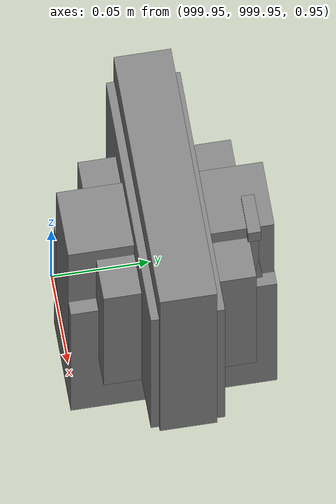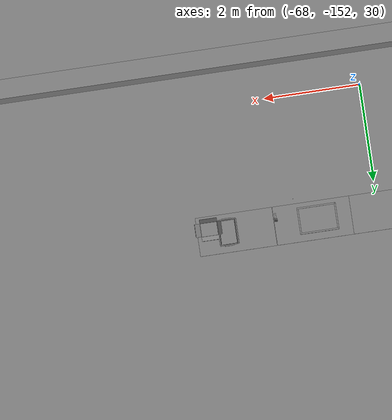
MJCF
<mujoco>
    <option gravity="0.000000000 0.000000000 -9.810000420" timestep="0.0049999999" integrator="implicitfast" density="1.225" viscosity="1.8000001e-05" noslip_iterations="10" iterations="100" sdf_iterations="50">
        <flag multiccd="disable"/>
    </option>
    <size memory="1000M"/>
    <compiler coordinate="local"/>
    <worldbody>
        <light cutoff="30" pos="0 1 1" dir="0 -1 -2"/>
        <light cutoff="30" pos="0 -1 1" dir="0 1 -2"/>
        <body pos="1000.000000000 1000.000000000 1.000000000" euler="0.000000000 0.000000000 180.000000000" name="openloong_gripper_2f85_fix_base_usda_wifi_box">
            <geom contype="1" conaffinity="1" density="1000" type="box" material="" rgba="0.500000000 0.500000000 0.500000000 1.000000000" solimp="0.899999976 0.949999988 0.001000000" friction="1.000000000 0.005000000 0.000100000" solref="0.020000000 1.000000000" margin="0" condim="3" group="0" pos="0.000000000 0.000000000 0.058978677" quat="0.000000000 0.000000047 0.000000000 1.000000000" size="0.068499997 0.018999999 0.059000000" name="openloong_gripper_2f85_fix_base_usda_geom_C703A186_1279_451E_864B_E0C9BB23E390"/>
            <freejoint name="openloong_gripper_2f85_fix_base_usda_wifi_box_joint"/>
            <site size="0.005000000 0.005000000 0.005000000" rgba="0.500000000 0.500000000 0.500000000 1.000000000" pos="0.000000000 0.000000000 0.000000000" quat="0.999961913 0.008726500 0.000000000 0.000000000" group="0" type="sphere" name="openloong_gripper_2f85_fix_base_usda_wifi_boxsite"/>
        </body>
        <body pos="1000.000000000 1000.000000000 1.000000000" euler="0.000000000 0.000000000 180.000000000" name="openloong_gripper_2f85_fix_base_usda_cpu_fan">
            <geom contype="1" conaffinity="1" density="1000" type="box" material="" rgba="0.500000000 0.500000000 0.500000000 1.000000000" solimp="0.899999976 0.949999988 0.001000000" friction="1.000000000 0.005000000 0.000100000" solref="0.020000000 1.000000000" margin="0" condim="3" group="0" pos="0.000000000 0.000000000 0.070034981" quat="0.000000000 0.000000000 0.000000000 1.000000000" size="0.070700005 0.014699999 0.070700005" name="openloong_gripper_2f85_fix_base_usda_geom_207C4D80_A94F_4479_A906_3117F4C9382F"/>
            <freejoint name="openloong_gripper_2f85_fix_base_usda_cpu_fan_joint"/>
            <site size="0.005000000 0.005000000 0.005000000" rgba="0.500000000 0.500000000 0.500000000 1.000000000" pos="0.000000000 0.000000000 0.000000000" quat="0.999961913 0.008726535 0.000000000 0.000000000" group="0" type="sphere" name="openloong_gripper_2f85_fix_base_usda_cpu_fancsite"/>
        </body>
        <body pos="1000.000000000 1000.000000000 1.000000000" euler="0.000000000 0.000000000 180.000000000" name="openloong_gripper_2f85_fix_base_usda_battery_01">
            <geom contype="1" conaffinity="1" density="1000" type="box" material="" rgba="0.500000000 0.500000000 0.500000000 1.000000000" solimp="0.899999976 0.949999988 0.001000000" friction="1.000000000 0.005000000 0.000100000" solref="0.020000000 1.000000000" margin="0" condim="3" group="0" pos="-0.011123657 -0.041940309 0.101691343" quat="1.000000000 0.000000000 0.000000000 0.000000000" size="0.010800000 0.003375000 0.004725000" name="openloong_gripper_2f85_fix_base_usda_geom_61F94120_405D_4047_842E_CCCF1323FBF3"/>
            <geom contype="1" conaffinity="1" density="1000" type="box" material="" rgba="0.500000000 0.500000000 0.500000000 1.000000000" solimp="0.899999976 0.949999988 0.001000000" friction="1.000000000 0.005000000 0.000100000" solref="0.020000000 1.000000000" margin="0" condim="3" group="0" pos="-0.010876465 -0.044247437 0.047066893" quat="0.998702705 -0.050920475 0.000000000 0.000000000" size="0.009450001 0.002700000 0.024975000" name="openloong_gripper_2f85_fix_base_usda_geom_B32CA99F_C36E_4BF2_B221_F4A00C4CAD30"/>
            <geom contype="1" conaffinity="1" density="1000" type="box" material="" rgba="0.500000000 0.500000000 0.500000000 1.000000000" solimp="0.899999976 0.949999988 0.001000000" friction="1.000000000 0.005000000 0.000100000" solref="0.020000000 1.000000000" margin="0" condim="3" group="0" pos="-0.001235962 -0.000659180 0.047381196" quat="1.000000000 0.000000000 0.000000000 0.000000000" size="0.039420001 0.039150000 0.047250003" name="openloong_gripper_2f85_fix_base_usda_geom_4C2169A1_827D_4705_83A6_184D96CAF1F3"/>
            <geom contype="1" conaffinity="1" density="1000" type="box" material="" rgba="0.500000000 0.500000000 0.500000000 1.000000000" solimp="0.899999976 0.949999988 0.001000000" friction="1.000000000 0.005000000 0.000100000" solref="0.020000000 1.000000000" margin="0" condim="3" group="0" pos="-0.010876465 -0.039138794 0.009851727" quat="1.000000000 0.000000000 0.000000000 0.000000000" size="0.009450001 0.010800000 0.013500000" name="openloong_gripper_2f85_fix_base_usda_geom_1749BAFA_4306_4E19_9881_ED8790847F91"/>
            <geom contype="1" conaffinity="1" density="1000" type="box" material="" rgba="0.500000000 0.500000000 0.500000000 1.000000000" solimp="0.899999976 0.949999988 0.001000000" friction="1.000000000 0.005000000 0.000100000" solref="0.020000000 1.000000000" margin="0" condim="3" group="0" pos="-0.010876465 -0.041528322 0.071508206" quat="1.000000000 0.000000000 0.000000000 0.000000000" size="0.009450001 0.002700000 0.027000001" name="openloong_gripper_2f85_fix_base_usda_geom_5485DBA5_908C_4A0B_BA46_3B8EA07CD4F7"/>
            <freejoint name="openloong_gripper_2f85_fix_base_usda_battery_01_joint"/>
            <site size="0.005000000 0.005000000 0.005000000" rgba="0.500000000 0.500000000 0.500000000 1.000000000" pos="0.000000000 0.000000000 0.000000000" quat="0.999961913 0.008726500 0.000000000 0.000000000" group="0" type="sphere" name="openloong_gripper_2f85_fix_base_usda_battery_01site"/>
        </body>
        <body pos="1000.000000000 1000.000000000 1.000000000" euler="0.000011953 0.000005123 -179.999984741" name="openloong_gripper_2f85_fix_base_usda_intel_box">
            <geom contype="1" conaffinity="1" density="1000" type="box" material="" rgba="0.500000000 0.500000000 0.500000000 1.000000000" solimp="0.899999976 0.949999988 0.001000000" friction="1.000000000 0.005000000 0.000100000" solref="0.020000000 1.000000000" margin="0" condim="3" group="0" pos="0.000000000 -0.000067139 0.000082284" quat="0.707106709 0.000000225 0.000000253 0.707106650" size="0.052800003 0.025300000 0.052800003" name="openloong_gripper_2f85_fix_base_usda_geom_5D7C88FD_363A_46BB_B08E_76FC08AE2139"/>
            <freejoint name="openloong_gripper_2f85_fix_base_usda_intel_box_joint"/>
            <site size="0.005000000 0.005000000 0.005000000" rgba="0.500000000 0.500000000 0.500000000 1.000000000" pos="0.000000000 0.000000000 0.000000000" quat="0.999961913 0.008726500 0.000000000 0.000000000" group="0" type="sphere" name="openloong_gripper_2f85_fix_base_usda_intel_boxsite"/>
        </body>
        <body pos="1000.000000000 999.999938965 1.000000000" euler="0.000000000 0.000000000 180.000000000" name="openloong_gripper_2f85_fix_base_usda_intelcore_i5">
            <geom contype="1" conaffinity="1" density="1000" type="box" material="" rgba="0.500000000 0.500000000 0.500000000 1.000000000" solimp="0.899999976 0.949999988 0.001000000" friction="1.000000000 0.005000000 0.000100000" solref="0.020000000 1.000000000" margin="0" condim="3" group="0" pos="0.000000000 0.000000000 0.051722717" quat="0.707106709 0.000000000 0.000000000 -0.707106769" size="0.052800000 0.018080002 0.052800000" name="openloong_gripper_2f85_fix_base_usda_geom_450B66E3_0BAF_42DE_AB96_39605D5EA7FD"/>
            <freejoint name="openloong_gripper_2f85_fix_base_usda_intelcore_i5_joint"/>
            <site size="0.005000000 0.005000000 0.005000000" rgba="0.500000000 0.500000000 0.500000000 1.000000000" pos="0.000000000 0.000000000 0.000000000" quat="0.999961913 0.008726534 0.000000000 0.000000000" group="0" type="sphere" name="openloong_gripper_2f85_fix_base_usda_intelcore_i5site"/>
        </body>
        <body pos="-66.331809998 -149.140869141 31.167896271" euler="79.471412659 8.720666885 -75.235229492" mocap="true" name="spotlight2_SpotLight"/>
        <body pos="-66.237182617 -148.993255615 31.163991928" euler="-44.000637054 17.899982452 74.930145264" mocap="true" name="spotlight1_SpotLight"/>
        <body pos="-65.840270996 -149.095306396 31.167446136" euler="38.294578552 -23.786081314 125.066917419" mocap="true" name="spotlight4_SpotLight"/>
        <body pos="-64.866622925 -149.383972168 30.183746338" euler="89.999984741 89.999946594 0.000000000" name="openloong_gripper_2f85_fix_base_usda_bluebox_01">
            <geom contype="1" conaffinity="1" density="1000" type="box" material="" rgba="0.500000000 0.500000000 0.500000000 1.000000000" solimp="0.899999976 0.949999988 0.001000000" friction="1.000000000 0.005000000 0.000100000" solref="0.020000000 1.000000000" margin="0" condim="3" group="0" pos="0.276580811 0.187225342 0.000068665" quat="0.707106948 0.000077471 0.707106352 0.000077486" size="0.100000001 0.057999998 0.010000000" name="openloong_gripper_2f85_fix_base_usda_geom_D0320D10_9BC1_41FC_9A4E_3B32A7793E7F"/>
            <geom contype="1" conaffinity="1" density="1000" type="box" material="" rgba="0.500000000 0.500000000 0.500000000 1.000000000" solimp="0.899999976 0.949999988 0.001000000" friction="1.000000000 0.005000000 0.000100000" solref="0.020000000 1.000000000" margin="0" condim="3" group="0" pos="0.000000000 0.002883911 0.000000000" quat="0.999999881 0.000000000 0.000000000 0.000000000" size="0.254000008 0.003000000 0.172000006" name="openloong_gripper_2f85_fix_base_usda_geom_8A59F9B3_35B3_4F5A_ADDE_E74465AFCFEC"/>
            <geom contype="1" conaffinity="1" density="1000" type="box" material="" rgba="0.500000000 0.500000000 0.500000000 1.000000000" solimp="0.899999976 0.949999988 0.001000000" friction="1.000000000 0.005000000 0.000100000" solref="0.020000000 1.000000000" margin="0" condim="3" group="0" pos="0.000000000 0.124874115 0.173484802" quat="0.999796331 0.020176515 -0.000000015 0.000000030" size="0.259999990 0.119999997 0.007000000" name="openloong_gripper_2f85_fix_base_usda_geom_3DF43EF5_5343_4A33_9AC7_2ECB3A15B452"/>
            <geom contype="1" conaffinity="1" density="1000" type="box" material="" rgba="0.500000000 0.500000000 0.500000000 1.000000000" solimp="0.899999976 0.949999988 0.001000000" friction="1.000000000 0.005000000 0.000100000" solref="0.020000000 1.000000000" margin="0" condim="3" group="0" pos="0.000000000 0.124874115 -0.173469543" quat="0.999796331 -0.020176545 -0.000000015 0.000000000" size="0.259999990 0.119999997 0.007000000" name="openloong_gripper_2f85_fix_base_usda_geom_ED74C3B0_C2DA_4FA0_8FBB_0BD56D0E3C70"/>
            <geom contype="1" conaffinity="1" density="1000" type="box" material="" rgba="0.500000000 0.500000000 0.500000000 1.000000000" solimp="0.899999976 0.949999988 0.001000000" friction="1.000000000 0.005000000 0.000100000" solref="0.020000000 1.000000000" margin="0" condim="3" group="0" pos="0.000000000 0.214008331 0.188980103" quat="0.999912977 0.013176724 0.000000015 0.000000000" size="0.259999990 0.029999999 0.012500000" name="openloong_gripper_2f85_fix_base_usda_geom_6E7BC5F1_3A96_4E9D_880E_637E93C99606"/>
            <geom contype="1" conaffinity="1" density="1000" type="box" material="" rgba="0.500000000 0.500000000 0.500000000 1.000000000" solimp="0.899999976 0.949999988 0.001000000" friction="1.000000000 0.005000000 0.000100000" solref="0.020000000 1.000000000" margin="0" condim="3" group="0" pos="-0.258361816 0.125289917 0.001876831" quat="0.702796936 -0.020792112 0.710783124 0.020769298" size="0.189999998 0.119999997 0.009000000" name="openloong_gripper_2f85_fix_base_usda_geom_6598D04B_779D_4EC9_BCE8_C684D5C10C50"/>
            <geom contype="1" conaffinity="1" density="1000" type="box" material="" rgba="0.500000000 0.500000000 0.500000000 1.000000000" solimp="0.899999976 0.949999988 0.001000000" friction="1.000000000 0.005000000 0.000100000" solref="0.020000000 1.000000000" margin="0" condim="3" group="0" pos="0.000000000 0.214008331 -0.188980103" quat="0.999912977 -0.013176769 0.000000030 0.000000015" size="0.259999990 0.029999999 0.012500000" name="openloong_gripper_2f85_fix_base_usda_geom_F2DF3EBB_9258_42BE_902C_51993E811595"/>
            <geom contype="1" conaffinity="1" density="1000" type="box" material="" rgba="0.500000000 0.500000000 0.500000000 1.000000000" solimp="0.899999976 0.949999988 0.001000000" friction="1.000000000 0.005000000 0.000100000" solref="0.020000000 1.000000000" margin="0" condim="3" group="0" pos="-0.276611328 0.187225342 0.000068665" quat="0.707106650 0.000077441 0.707106709 0.000077456" size="0.100000001 0.057999998 0.010000000" name="openloong_gripper_2f85_fix_base_usda_geom_DB096AD1_40A1_4F8E_B302_00FAADDD8212"/>
            <geom contype="1" conaffinity="1" density="1000" type="box" material="" rgba="0.500000000 0.500000000 0.500000000 1.000000000" solimp="0.899999976 0.949999988 0.001000000" friction="1.000000000 0.005000000 0.000100000" solref="0.020000000 1.000000000" margin="0" condim="3" group="0" pos="0.258331299 0.125289917 0.001876831" quat="0.702851415 0.018856421 0.710823774 -0.019329369" size="0.189999998 0.119999997 0.009000000" name="openloong_gripper_2f85_fix_base_usda_geom_4D66C7C4_F6A1_44C6_B519_3012954AD29E"/>
            <freejoint name="openloong_gripper_2f85_fix_base_usda_bluebox_01_joint"/>
            <site size="0.005000000 0.005000000 0.005000000" rgba="0.500000000 0.500000000 0.500000000 1.000000000" pos="0.000000000 0.000000000 0.000000000" quat="0.999961913 0.008726534 0.000000000 0.000000000" group="0" type="sphere" name="openloong_gripper_2f85_fix_base_usda_bluebox_01site"/>
        </body>
        <body pos="-64.496299744 -149.491867065 30.235729218" euler="0.000000000 0.000000000 89.999946594" name="openloong_gripper_2f85_fix_base_usda_cardboardbox_01">
            <geom contype="1" conaffinity="1" density="1000" type="box" material="" rgba="0.500000000 0.500000000 0.500000000 1.000000000" solimp="0.899999976 0.949999988 0.001000000" friction="1.000000000 0.005000000 0.000100000" solref="0.020000000 1.000000000" margin="0" condim="3" group="0" pos="-0.003166199 -0.004086494 0.005052090" quat="1.000000000 0.000000000 0.000000000 0.000000000" size="0.142499998 0.177500010 0.005000000" name="openloong_gripper_2f85_fix_base_usda_geom_722D8FE1_E9A3_4C6C_B6E8_C716D4AF6801"/>
            <geom contype="1" conaffinity="1" density="1000" type="box" material="" rgba="0.500000000 0.500000000 0.500000000 1.000000000" solimp="0.899999976 0.949999988 0.001000000" friction="1.000000000 0.005000000 0.000100000" solref="0.020000000 1.000000000" margin="0" condim="3" group="0" pos="-0.003166199 0.170316696 0.150570869" quat="1.000000000 0.000000000 0.000000000 0.000000000" size="0.142499998 0.005000000 0.149999991" name="openloong_gripper_2f85_fix_base_usda_geom_F5D4DD8D_F3A8_4AFF_9516_7AA463B1C19B"/>
            <geom contype="1" conaffinity="1" density="1000" type="box" material="" rgba="0.500000000 0.500000000 0.500000000 1.000000000" solimp="0.899999976 0.949999988 0.001000000" friction="1.000000000 0.005000000 0.000100000" solref="0.020000000 1.000000000" margin="0" condim="3" group="0" pos="-0.147399902 -0.005307198 0.150570869" quat="1.000000000 0.000000000 0.000000000 0.000000000" size="0.005000000 0.177500010 0.149999991" name="openloong_gripper_2f85_fix_base_usda_geom_ED517D69_CB45_4695_960B_AA08BC5B6EC1"/>
            <geom contype="1" conaffinity="1" density="1000" type="box" material="" rgba="0.500000000 0.500000000 0.500000000 1.000000000" solimp="0.899999976 0.949999988 0.001000000" friction="1.000000000 0.005000000 0.000100000" solref="0.020000000 1.000000000" margin="0" condim="3" group="0" pos="0.140275955 -0.005307198 0.150570869" quat="1.000000000 0.000000000 0.000000000 0.000000000" size="0.005000000 0.177500010 0.149999991" name="openloong_gripper_2f85_fix_base_usda_geom_5E588950_F2EF_4DFE_A81D_0E803C706790"/>
            <geom contype="1" conaffinity="1" density="1000" type="box" material="" rgba="0.500000000 0.500000000 0.500000000 1.000000000" solimp="0.899999976 0.949999988 0.001000000" friction="1.000000000 0.005000000 0.000100000" solref="0.020000000 1.000000000" margin="0" condim="3" group="0" pos="-0.003166199 -0.181550980 0.150570869" quat="1.000000000 0.000000000 0.000000000 0.000000000" size="0.142499998 0.005000000 0.149999991" name="openloong_gripper_2f85_fix_base_usda_geom_EFC221E7_7E20_489A_B1CD_05FF6E3DCF47"/>
            <freejoint name="openloong_gripper_2f85_fix_base_usda_cardboardbox_01_joint"/>
            <site size="0.005000000 0.005000000 0.005000000" rgba="0.500000000 0.500000000 0.500000000 1.000000000" pos="0.000000000 0.000000000 0.000000000" quat="0.999961913 0.008726535 0.000000000 0.000000000" group="0" type="sphere" name="openloong_gripper_2f85_fix_base_usda_site_52A8BD4F_A651_4391_A47F_1C7F18F921C0"/>
            <body pos="0.139160156 -0.004048347 0.301930904" euler="-179.999954224 49.383502960 179.999954224" name="openloong_gripper_2f85_fix_base_usda_A1_006">
                <geom contype="1" conaffinity="1" density="1000" type="box" material="" rgba="0.500000000 0.500000000 0.500000000 1.000000000" solimp="0.899999976 0.949999988 0.001000000" friction="1.000000000 0.005000000 0.000100000" solref="0.020000000 1.000000000" margin="0" condim="3" group="0" pos="-0.071587563 0.000009537 0.001745224" quat="0.999999881 0.000000000 0.000000000 0.000000000" size="0.071249999 0.179999992 0.002500000" name="openloong_gripper_2f85_fix_base_usda_geom_5F5F0637_CDCB_4916_946E_6377660151DF"/>
                <joint armature="0" stiffness="0.07" damping="0.0099999998" axis="0.000000 1.000000 0.000000" type="hinge" name="openloong_gripper_2f85_fix_base_usda_A1_006"/>
            </body>
            <body pos="-0.145902634 -0.004086494 0.301938057" euler="-180.000000000 -60.000011444 -180.000000000" name="openloong_gripper_2f85_fix_base_usda_A2_006">
                <geom contype="1" conaffinity="1" density="1000" type="box" material="" rgba="0.500000000 0.500000000 0.500000000 1.000000000" solimp="0.899999976 0.949999988 0.001000000" friction="1.000000000 0.005000000 0.000100000" solref="0.020000000 1.000000000" margin="0" condim="3" group="0" pos="0.071268082 0.000009537 0.002717972" quat="0.000002921 0.000000000 -0.000000030 0.999999881" size="0.071249999 0.179999992 0.002500000" name="openloong_gripper_2f85_fix_base_usda_geom_0F8BCCC7_CCEE_4115_96B8_018776381536"/>
                <joint armature="0" stiffness="0.07" damping="0.0099999998" axis="0.000000 1.000000 0.000000" type="hinge" name="openloong_gripper_2f85_fix_base_usda_A2_006"/>
            </body>
            <body pos="-0.003385544 0.175991058 0.301930904" euler="-125.858116150 -0.000004561 0.000002331" name="openloong_gripper_2f85_fix_base_usda_B2_006">
                <geom contype="1" conaffinity="1" density="1000" type="box" material="" rgba="0.500000000 0.500000000 0.500000000 1.000000000" solimp="0.899999976 0.949999988 0.001000000" friction="1.000000000 0.005000000 0.000100000" solref="0.020000000 1.000000000" margin="0" condim="3" group="0" pos="0.000009537 -0.070939064 -0.002470016" quat="0.999614120 0.027776197 -0.000000015 0.000000030" size="0.137500003 0.064999998 0.005000000" name="openloong_gripper_2f85_fix_base_usda_geom_0BF2F783_469F_4FAF_9C1B_E69422206141"/>
                <joint armature="0" stiffness="0.07" damping="0.0099999998" axis="1.000000 0.000000 0.000000" type="hinge" name="openloong_gripper_2f85_fix_base_usda_B2_006"/>
            </body>
            <body pos="-0.003385544 -0.184140205 0.301938057" euler="147.805557251 0.000000000 0.000000000" name="openloong_gripper_2f85_fix_base_usda_B1_006">
                <geom contype="1" conaffinity="1" density="1000" type="box" material="" rgba="0.500000000 0.500000000 0.500000000 1.000000000" solimp="0.899999976 0.949999988 0.001000000" friction="1.000000000 0.005000000 0.000100000" solref="0.020000000 1.000000000" margin="0" condim="3" group="0" pos="-0.000028610 0.070202351 -0.002703667" quat="0.999614179 -0.027776167 0.000000000 0.000000000" size="0.137500003 0.064999998 0.005000000" name="openloong_gripper_2f85_fix_base_usda_geom_62B3BFAF_61E1_4EC8_952C_5D2C402B69C1"/>
                <joint armature="0" stiffness="0.07" damping="0.0099999998" axis="1.000000 0.000000 0.000000" type="hinge" name="openloong_gripper_2f85_fix_base_usda_B1_006"/>
            </body>
        </body>
        <body pos="-65.882858276 -149.481979370 30.229999542" euler="-64.487716675 0.000000000 0.000000000" name="openloong_gripper_2f85_fix_base_usda_Barcode">
            <geom contype="1" conaffinity="1" density="1000" type="box" material="" rgba="0.500000000 0.500000000 0.500000000 1.000000000" solimp="0.899999976 0.949999988 0.001000000" friction="1.000000000 0.005000000 0.000100000" solref="0.020000000 1.000000000" margin="0" condim="3" group="0" pos="0.000000000 0.013038635 0.001419067" quat="0.000000000 0.000000000 0.000000000 1.000000119" size="0.034000002 0.010000000 0.017999999" name="openloong_gripper_2f85_fix_base_usda_geom_3D0D5E87_3D0C_4D91_A607_6197AA49C752"/>
            <geom contype="1" conaffinity="1" density="1000" type="box" material="" rgba="0.500000000 0.500000000 0.500000000 1.000000000" solimp="0.899999976 0.949999988 0.001000000" friction="1.000000000 0.005000000 0.000100000" solref="0.020000000 1.000000000" margin="0" condim="3" group="0" pos="0.000000000 -0.035301208 -0.007095337" quat="0.000000000 0.000000000 -0.043619365 0.999048233" size="0.028999999 0.010000000 0.020000000" name="openloong_gripper_2f85_fix_base_usda_geom_D70AFC1C_F650_4BA2_BBA0_241373976818"/>
            <geom contype="1" conaffinity="1" density="1000" type="box" material="" rgba="0.500000000 0.500000000 0.500000000 1.000000000" solimp="0.899999976 0.949999988 0.001000000" friction="1.000000000 0.005000000 0.000100000" solref="0.020000000 1.000000000" margin="0" condim="3" group="0" pos="0.000000000 -0.043411255 -0.011749268" quat="0.922262907 0.386563420 0.000000000 0.000000000" size="0.026000001 0.010000000 0.020000000" name="openloong_gripper_2f85_fix_base_usda_geom_D8411E91_8E6E_4458_A566_D8E3C8CF2CFE"/>
            <geom contype="1" conaffinity="1" density="1000" type="box" material="" rgba="0.500000000 0.500000000 0.500000000 1.000000000" solimp="0.899999976 0.949999988 0.001000000" friction="1.000000000 0.005000000 0.000100000" solref="0.020000000 1.000000000" margin="0" condim="3" group="0" pos="0.000000000 -0.016967773 -0.031860352" quat="0.000000000 0.000000000 0.000000000 1.000000119" size="0.008000000 0.010000000 0.013000000" name="openloong_gripper_2f85_fix_base_usda_geom_EB4DF2D4_6617_491F_8E36_2D6B50454CC3"/>
            <geom contype="1" conaffinity="1" density="1000" type="box" material="" rgba="0.500000000 0.500000000 0.500000000 1.000000000" solimp="0.899999976 0.949999988 0.001000000" friction="1.000000000 0.005000000 0.000100000" solref="0.020000000 1.000000000" margin="0" condim="3" group="0" pos="0.000000000 -0.001869202 0.000312805" quat="0.953716993 0.300705761 0.000000000 0.000000000" size="0.032000002 0.010000000 0.018999999" name="openloong_gripper_2f85_fix_base_usda_geom_FC276A68_F284_40BC_B917_48AB7C22512C"/>
            <geom contype="1" conaffinity="1" density="1000" type="box" material="" rgba="0.500000000 0.500000000 0.500000000 1.000000000" solimp="0.899999976 0.949999988 0.001000000" friction="1.000000000 0.005000000 0.000100000" solref="0.020000000 1.000000000" margin="0" condim="3" group="0" pos="0.000000000 -0.019531250 -0.003173828" quat="0.953716993 0.300705761 0.000000000 0.000000000" size="0.030999999 0.010000000 0.020000000" name="openloong_gripper_2f85_fix_base_usda_geom_5A38BA07_DD38_4CCB_8836_FA2DBBBC5E80"/>
            <geom contype="1" conaffinity="1" density="1000" type="box" material="" rgba="0.500000000 0.500000000 0.500000000 1.000000000" solimp="0.899999976 0.949999988 0.001000000" friction="1.000000000 0.005000000 0.000100000" solref="0.020000000 1.000000000" margin="0" condim="3" group="0" pos="0.000000000 -0.035301208 -0.007095337" quat="0.953716993 0.300705761 0.000000000 0.000000000" size="0.028999999 0.010000000 0.020000000" name="openloong_gripper_2f85_fix_base_usda_geom_49F30B79_A496_485A_B3A4_DCCEE2E70D6D"/>
            <geom contype="1" conaffinity="1" density="1000" type="box" material="" rgba="0.500000000 0.500000000 0.500000000 1.000000000" solimp="0.899999976 0.949999988 0.001000000" friction="1.000000000 0.005000000 0.000100000" solref="0.020000000 1.000000000" margin="0" condim="3" group="0" pos="0.000000000 -0.042617798 -0.071121216" quat="0.000000000 0.000000000 0.000000000 1.000000119" size="0.013000000 0.021000000 0.059999999" name="openloong_gripper_2f85_fix_base_usda_geom_1CAF78E9_B63B_40A9_B19A_346D9FEC7CF3"/>
            <freejoint name="openloong_gripper_2f85_fix_base_usda_Barcode_joint"/>
            <site size="0.005000000 0.005000000 0.005000000" rgba="0.500000000 0.500000000 0.500000000 1.000000000" pos="0.000000000 0.000000000 0.000000000" quat="1.000000000 0.000000000 0.000000000 0.000000000" group="0" type="sphere" name="openloong_gripper_2f85_fix_base_usda_Barcode_site"/>
        </body>
        <body pos="-66.745018005 -149.392349243 30.184000015" euler="0.000000000 0.000000000 89.999946594" name="[22331286154149]_Basket_01">
            <geom contype="1" conaffinity="1" density="1000" type="box" material="" rgba="0.500000000 0.500000000 0.500000000 1.000000000" solimp="0.899999976 0.949999988 0.001000000" friction="1.000000000 0.005000000 0.000100000" solref="0.020000000 1.000000000" margin="0" condim="3" group="0" pos="-0.052425385 0.389207840 0.089787483" quat="0.707107008 0.000000000 0.000000000 0.707106411" size="0.014249999 0.014249999 0.059999999" name="[22331286154149]_geom_49C897E4_F0F9_4223_824E_A9A0193F14C3"/>
            <geom contype="1" conaffinity="1" density="1000" type="box" material="" rgba="0.500000000 0.500000000 0.500000000 1.000000000" solimp="0.899999976 0.949999988 0.001000000" friction="1.000000000 0.005000000 0.000100000" solref="0.020000000 1.000000000" margin="0" condim="3" group="0" pos="0.264015198 -0.133043289 0.089787483" quat="0.707107008 0.000000000 0.000000000 0.707106411" size="0.014249999 0.014249999 0.059999999" name="[22331286154149]_geom_09364F61_41D2_4D6D_9BB6_469BA76F79B3"/>
            <geom contype="1" conaffinity="1" density="1000" type="box" material="" rgba="0.500000000 0.500000000 0.500000000 1.000000000" solimp="0.899999976 0.949999988 0.001000000" friction="1.000000000 0.005000000 0.000100000" solref="0.020000000 1.000000000" margin="0" condim="3" group="0" pos="-0.264015198 -0.265548706 0.089793205" quat="0.707107008 0.000000000 0.000000000 0.707106411" size="0.014249999 0.014249999 0.059999999" name="[22331286154149]_geom_A8203AAF_16A0_4A6E_BEDD_0D74483DC988"/>
            <geom contype="1" conaffinity="1" density="1000" type="box" material="" rgba="0.500000000 0.500000000 0.500000000 1.000000000" solimp="0.899999976 0.949999988 0.001000000" friction="1.000000000 0.005000000 0.000100000" solref="0.020000000 1.000000000" margin="0" condim="3" group="0" pos="-0.160263062 -0.389322281 0.089793205" quat="0.707107008 0.000000000 0.000000000 0.707106411" size="0.014249999 0.014249999 0.059999999" name="[22331286154149]_geom_6DAF591F_C070_4C3E_BA4B_BF36C6420806"/>
            <geom contype="1" conaffinity="1" density="1000" type="box" material="" rgba="0.500000000 0.500000000 0.500000000 1.000000000" solimp="0.899999976 0.949999988 0.001000000" friction="1.000000000 0.005000000 0.000100000" solref="0.020000000 1.000000000" margin="0" condim="3" group="0" pos="0.162265778 -0.389322281 0.089787483" quat="0.707107008 0.000000000 0.000000000 0.707106411" size="0.014249999 0.014249999 0.059999999" name="[22331286154149]_geom_6718522E_5C1A_457C_9EDB_08189F8E2A64"/>
            <geom contype="1" conaffinity="1" density="1000" type="box" material="" rgba="0.500000000 0.500000000 0.500000000 1.000000000" solimp="0.899999976 0.949999988 0.001000000" friction="1.000000000 0.005000000 0.000100000" solref="0.020000000 1.000000000" margin="0" condim="3" group="0" pos="0.264015198 0.389207840 0.089787483" quat="0.707107008 0.000000000 0.000000000 0.707106411" size="0.014249999 0.014249999 0.059999999" name="[22331286154149]_geom_B7BC9782_139C_4CBD_B24A_BF986764CEC8"/>
            <geom contype="1" conaffinity="1" density="1000" type="box" material="" rgba="0.500000000 0.500000000 0.500000000 1.000000000" solimp="0.899999976 0.949999988 0.001000000" friction="1.000000000 0.005000000 0.000100000" solref="0.020000000 1.000000000" margin="0" condim="3" group="0" pos="-0.264015198 -0.133043289 0.089793205" quat="0.707107008 0.000000000 0.000000000 0.707106411" size="0.014249999 0.014249999 0.059999999" name="[22331286154149]_geom_F47CF2DE_4D22_43AB_8F44_7F90396B0A65"/>
            <geom contype="1" conaffinity="1" density="1000" type="box" material="" rgba="0.500000000 0.500000000 0.500000000 1.000000000" solimp="0.899999976 0.949999988 0.001000000" friction="1.000000000 0.005000000 0.000100000" solref="0.020000000 1.000000000" margin="0" condim="3" group="0" pos="-0.264026642 0.269256592 0.089793205" quat="0.707107008 0.000000000 0.000000000 0.707106411" size="0.014249999 0.014249999 0.059999999" name="[22331286154149]_geom_A2C9568C_AE2A_4D98_B80F_D150D951302A"/>
            <geom contype="1" conaffinity="1" density="1000" type="box" material="" rgba="0.500000000 0.500000000 0.500000000 1.000000000" solimp="0.899999976 0.949999988 0.001000000" friction="1.000000000 0.005000000 0.000100000" solref="0.020000000 1.000000000" margin="0" condim="3" group="0" pos="0.054462433 0.389207840 0.089787483" quat="0.707107008 0.000000000 0.000000000 0.707106411" size="0.014249999 0.014249999 0.059999999" name="[22331286154149]_geom_806ADE8F_43B5_41C2_8B88_C8FB97401DD3"/>
            <geom contype="1" conaffinity="1" density="1000" type="box" material="" rgba="0.500000000 0.500000000 0.500000000 1.000000000" solimp="0.899999976 0.949999988 0.001000000" friction="1.000000000 0.005000000 0.000100000" solref="0.020000000 1.000000000" margin="0" condim="3" group="0" pos="0.054462433 -0.389322281 0.089787483" quat="0.707107008 0.000000000 0.000000000 0.707106411" size="0.014249999 0.014249999 0.059999999" name="[22331286154149]_geom_388BBCED_532F_426E_95C4_36C025AC50AB"/>
            <geom contype="1" conaffinity="1" density="1000" type="box" material="" rgba="0.500000000 0.500000000 0.500000000 1.000000000" solimp="0.899999976 0.949999988 0.001000000" friction="1.000000000 0.005000000 0.000100000" solref="0.020000000 1.000000000" margin="0" condim="3" group="0" pos="0.264015198 0.269256592 0.089793205" quat="0.707107008 0.000000000 0.000000000 0.707106411" size="0.014249999 0.014249999 0.059999999" name="[22331286154149]_geom_D4DB6B60_B536_42DA_BA4A_C57B7F989B63"/>
            <geom contype="1" conaffinity="1" density="1000" type="box" material="" rgba="0.500000000 0.500000000 0.500000000 1.000000000" solimp="0.899999976 0.949999988 0.001000000" friction="1.000000000 0.005000000 0.000100000" solref="0.020000000 1.000000000" margin="0" condim="3" group="0" pos="0.264015198 -0.389322281 0.089787483" quat="0.707107008 0.000000000 0.000000000 0.707106411" size="0.014249999 0.014249999 0.059999999" name="[22331286154149]_geom_07971904_04E7_4FB4_8A9C_32DA05413E1D"/>
            <geom contype="1" conaffinity="1" density="1000" type="box" material="" rgba="0.500000000 0.500000000 0.500000000 1.000000000" solimp="0.899999976 0.949999988 0.001000000" friction="1.000000000 0.005000000 0.000100000" solref="0.020000000 1.000000000" margin="0" condim="3" group="0" pos="0.000000000 0.000000000 0.015998840" quat="0.707107008 0.000000000 0.000000000 0.707106411" size="0.403499991 0.279000014 0.015750000" name="[22331286154149]_geom_2849FC55_E2C2_4B4B_A772_7A2AF8F68F90"/>
            <geom contype="1" conaffinity="1" density="1000" type="box" material="" rgba="0.500000000 0.500000000 0.500000000 1.000000000" solimp="0.899999976 0.949999988 0.001000000" friction="1.000000000 0.005000000 0.000100000" solref="0.020000000 1.000000000" margin="0" condim="3" group="0" pos="0.000000000 -0.389476776 0.163619041" quat="0.707107008 0.000000000 0.000000000 0.707106411" size="0.015000000 0.277500004 0.015750000" name="[22331286154149]_geom_041FD985_9280_4472_AE9D_7F7889462744"/>
            <geom contype="1" conaffinity="1" density="1000" type="box" material="" rgba="0.500000000 0.500000000 0.500000000 1.000000000" solimp="0.899999976 0.949999988 0.001000000" friction="1.000000000 0.005000000 0.000100000" solref="0.020000000 1.000000000" margin="0" condim="3" group="0" pos="0.162265778 0.389207840 0.089787483" quat="0.707107008 0.000000000 0.000000000 0.707106411" size="0.014249999 0.014249999 0.059999999" name="[22331286154149]_geom_AB5DC692_D8C0_4C75_89E7_6286CE0ED4BB"/>
            <geom contype="1" conaffinity="1" density="1000" type="box" material="" rgba="0.500000000 0.500000000 0.500000000 1.000000000" solimp="0.899999976 0.949999988 0.001000000" friction="1.000000000 0.005000000 0.000100000" solref="0.020000000 1.000000000" margin="0" condim="3" group="0" pos="0.000000000 0.389471054 0.163619041" quat="0.707107008 0.000000000 0.000000000 0.707106411" size="0.015000000 0.277500004 0.015750000" name="[22331286154149]_geom_7B66359C_C191_4006_A6B9_69D5ED76F437"/>
            <geom contype="1" conaffinity="1" density="1000" type="box" material="" rgba="0.500000000 0.500000000 0.500000000 1.000000000" solimp="0.899999976 0.949999988 0.001000000" friction="1.000000000 0.005000000 0.000100000" solref="0.020000000 1.000000000" margin="0" condim="3" group="0" pos="-0.263511658 0.000000000 0.163619041" quat="0.707107008 0.000000000 0.000000000 0.707106411" size="0.403499991 0.015000000 0.015750000" name="[22331286154149]_geom_B9665253_257F_4A57_92CA_7605CBF5B802"/>
            <geom contype="1" conaffinity="1" density="1000" type="box" material="" rgba="0.500000000 0.500000000 0.500000000 1.000000000" solimp="0.899999976 0.949999988 0.001000000" friction="1.000000000 0.005000000 0.000100000" solref="0.020000000 1.000000000" margin="0" condim="3" group="0" pos="-0.264015198 0.141334534 0.089793205" quat="0.707107008 0.000000000 0.000000000 0.707106411" size="0.014249999 0.014249999 0.059999999" name="[22331286154149]_geom_1E5B929F_3150_4540_B4B6_D067D87D6DC3"/>
            <geom contype="1" conaffinity="1" density="1000" type="box" material="" rgba="0.500000000 0.500000000 0.500000000 1.000000000" solimp="0.899999976 0.949999988 0.001000000" friction="1.000000000 0.005000000 0.000100000" solref="0.020000000 1.000000000" margin="0" condim="3" group="0" pos="0.264015198 -0.265548706 0.089787483" quat="0.707107008 0.000000000 0.000000000 0.707106411" size="0.014249999 0.014249999 0.059999999" name="[22331286154149]_geom_3B35124D_1280_4351_8CB3_FA3CB1A18848"/>
            <geom contype="1" conaffinity="1" density="1000" type="box" material="" rgba="0.500000000 0.500000000 0.500000000 1.000000000" solimp="0.899999976 0.949999988 0.001000000" friction="1.000000000 0.005000000 0.000100000" solref="0.020000000 1.000000000" margin="0" condim="3" group="0" pos="-0.160263062 0.389207840 0.089787483" quat="0.707107008 0.000000000 0.000000000 0.707106411" size="0.014249999 0.014249999 0.059999999" name="[22331286154149]_geom_0118F8A6_A2FB_412B_B392_D6533B01D749"/>
            <geom contype="1" conaffinity="1" density="1000" type="box" material="" rgba="0.500000000 0.500000000 0.500000000 1.000000000" solimp="0.899999976 0.949999988 0.001000000" friction="1.000000000 0.005000000 0.000100000" solref="0.020000000 1.000000000" margin="0" condim="3" group="0" pos="-0.052425385 -0.389322281 0.089787483" quat="0.707107008 0.000000000 0.000000000 0.707106411" size="0.014249999 0.014249999 0.059999999" name="[22331286154149]_geom_AFF03BC9_4038_40B2_80B9_AB3ADEA1FF71"/>
            <geom contype="1" conaffinity="1" density="1000" type="box" material="" rgba="0.500000000 0.500000000 0.500000000 1.000000000" solimp="0.899999976 0.949999988 0.001000000" friction="1.000000000 0.005000000 0.000100000" solref="0.020000000 1.000000000" margin="0" condim="3" group="0" pos="-0.264026642 -0.389322281 0.089793205" quat="0.707107008 0.000000000 0.000000000 0.707106411" size="0.014249999 0.014249999 0.059999999" name="[22331286154149]_geom_1FE4BC5D_81C9_443E_B635_0EFC3505D210"/>
            <geom contype="1" conaffinity="1" density="1000" type="box" material="" rgba="0.500000000 0.500000000 0.500000000 1.000000000" solimp="0.899999976 0.949999988 0.001000000" friction="1.000000000 0.005000000 0.000100000" solref="0.020000000 1.000000000" margin="0" condim="3" group="0" pos="0.264015198 0.141334534 0.089787483" quat="0.707107008 0.000000000 0.000000000 0.707106411" size="0.014249999 0.014249999 0.059999999" name="[22331286154149]_geom_02D93942_89A7_4CEC_BEE1_EBB1A47765E0"/>
            <geom contype="1" conaffinity="1" density="1000" type="box" material="" rgba="0.500000000 0.500000000 0.500000000 1.000000000" solimp="0.899999976 0.949999988 0.001000000" friction="1.000000000 0.005000000 0.000100000" solref="0.020000000 1.000000000" margin="0" condim="3" group="0" pos="-0.264015198 0.389207840 0.089793205" quat="0.707107008 0.000000000 0.000000000 0.707106411" size="0.014249999 0.014249999 0.059999999" name="[22331286154149]_geom_FF092A21_70E0_4E2A_8E9F_339B634DBA7E"/>
            <geom contype="1" conaffinity="1" density="1000" type="box" material="" rgba="0.500000000 0.500000000 0.500000000 1.000000000" solimp="0.899999976 0.949999988 0.001000000" friction="1.000000000 0.005000000 0.000100000" solref="0.020000000 1.000000000" margin="0" condim="3" group="0" pos="0.264015198 0.004480362 0.089787483" quat="0.707107008 0.000000000 0.000000000 0.707106411" size="0.014249999 0.014249999 0.059999999" name="[22331286154149]_geom_8F121D85_BECB_413A_8168_77D17E588CDF"/>
            <geom contype="1" conaffinity="1" density="1000" type="box" material="" rgba="0.500000000 0.500000000 0.500000000 1.000000000" solimp="0.899999976 0.949999988 0.001000000" friction="1.000000000 0.005000000 0.000100000" solref="0.020000000 1.000000000" margin="0" condim="3" group="0" pos="0.263694763 -0.000011444 0.163619041" quat="0.707107008 0.000000000 0.000000000 0.707106411" size="0.403499991 0.015000000 0.015750000" name="[22331286154149]_geom_0F2F09CA_F350_4ACB_9C2C_565456A6B594"/>
            <geom contype="1" conaffinity="1" density="1000" type="box" material="" rgba="0.500000000 0.500000000 0.500000000 1.000000000" solimp="0.899999976 0.949999988 0.001000000" friction="1.000000000 0.005000000 0.000100000" solref="0.020000000 1.000000000" margin="0" condim="3" group="0" pos="-0.264015198 0.004480362 0.089793205" quat="0.707107008 0.000000000 0.000000000 0.707106411" size="0.014249999 0.014249999 0.059999999" name="[22331286154149]_geom_311D0E63_5E9A_43D2_93A2_B59CAAA788AD"/>
            <freejoint name="[22331286154149]_joint_B1DEFCE0_CD9F_4546_9212_0C47DDC205D5"/>
        </body>
        <body pos="0.000000000 0.000000000 0.000000000" euler="0.000000000 0.000000000 0.000000000" name="Static Objects_Static Objects">
            <geom contype="1" conaffinity="1" density="1000" type="box" material="" rgba="0.500000000 0.500000000 0.500000000 1.000000000" solimp="0.899999976 0.949999988 0.001000000" friction="1.000000000 0.005000000 0.000100000" solref="0.020000000 1.000000000" margin="0" condim="3" group="0" pos="-67.544113159 -149.365814209 29.727830887" quat="0.500000417 0.499999970 0.499999553 0.499999970" size="0.381000012 0.319999993 0.041000001" name="Static Objects_geom_1F9BC7E5_2225_465C_952D_2C48BB0CED30"/>
            <geom contype="1" conaffinity="1" density="1000" type="box" material="" rgba="0.500000000 0.500000000 0.500000000 1.000000000" solimp="0.899999976 0.949999988 0.001000000" friction="1.000000000 0.005000000 0.000100000" solref="0.020000000 1.000000000" margin="0" condim="3" group="0" pos="-68.239501953 -149.365814209 30.086868286" quat="0.500000417 0.499999970 0.499999553 0.499999970" size="0.370999992 0.039500002 0.745000005" name="Static Objects_geom_CFC03021_BE50_4892_A673_84790328AB97"/>
            <geom contype="1" conaffinity="1" density="1000" type="box" material="" rgba="0.500000000 0.500000000 0.500000000 1.000000000" solimp="0.899999976 0.949999988 0.001000000" friction="1.000000000 0.005000000 0.000100000" solref="0.020000000 1.000000000" margin="0" condim="3" group="0" pos="-68.239501953 -149.365814209 30.147235870" quat="0.500000417 0.499999970 0.499999553 0.499999970" size="0.400000006 0.022000000 0.800000012" name="Static Objects_geom_7C3559B4_EC24_4C13_8453_08C52919FFC9"/>
            <geom contype="1" conaffinity="1" density="1000" type="box" material="" rgba="0.500000000 0.500000000 0.500000000 1.000000000" solimp="0.899999976 0.949999988 0.001000000" friction="1.000000000 0.005000000 0.000100000" solref="0.020000000 1.000000000" margin="0" condim="3" group="0" pos="-68.934890747 -149.365814209 29.727830887" quat="0.500000417 0.499999970 0.499999553 0.499999970" size="0.381000012 0.319999993 0.041000001" name="Static Objects_geom_90F0E67A_3CAB_4477_8049_106001F47079"/>
            <geom contype="1" conaffinity="1" density="1000" type="box" material="" rgba="0.500000000 0.500000000 0.500000000 1.000000000" solimp="0.899999976 0.949999988 0.001000000" friction="1.000000000 0.005000000 0.000100000" solref="0.020000000 1.000000000" margin="0" condim="3" group="0" pos="-68.239501953 -149.365814209 29.561563492" quat="0.500000417 0.499999970 0.499999553 0.499999970" size="0.020000000 0.022000000 0.660000026" name="Static Objects_geom_F6CAE4A7_4B2B_4BAB_B29E_5484BFDE8108"/>
            <geom contype="1" conaffinity="1" density="1000" type="box" material="" rgba="0.500000000 0.500000000 0.500000000 1.000000000" solimp="0.899999976 0.949999988 0.001000000" friction="1.000000000 0.005000000 0.000100000" solref="0.020000000 1.000000000" margin="0" condim="3" group="0" pos="-65.945671082 -149.365814209 29.727830887" quat="0.500000417 0.499999970 0.499999553 0.499999970" size="0.381000012 0.319999993 0.041000001" name="Static Objects_geom_F6204E71_74F6_49BF_9C94_747C9C7988BC"/>
            <geom contype="1" conaffinity="1" density="1000" type="box" material="" rgba="0.500000000 0.500000000 0.500000000 1.000000000" solimp="0.899999976 0.949999988 0.001000000" friction="1.000000000 0.005000000 0.000100000" solref="0.020000000 1.000000000" margin="0" condim="3" group="0" pos="-66.641059875 -149.365814209 30.086868286" quat="0.500000417 0.499999970 0.499999553 0.499999970" size="0.370999992 0.039500002 0.745000005" name="Static Objects_geom_F4EFED9C_4022_4114_8807_6A3EFCFC9297"/>
            <geom contype="1" conaffinity="1" density="1000" type="box" material="" rgba="0.500000000 0.500000000 0.500000000 1.000000000" solimp="0.899999976 0.949999988 0.001000000" friction="1.000000000 0.005000000 0.000100000" solref="0.020000000 1.000000000" margin="0" condim="3" group="0" pos="-66.641059875 -149.365814209 30.147235870" quat="0.500000417 0.499999970 0.499999553 0.499999970" size="0.400000006 0.022000000 0.800000012" name="Static Objects_geom_86BC550F_C951_4DB7_9653_FED2CBC1154D"/>
            <geom contype="1" conaffinity="1" density="1000" type="box" material="" rgba="0.500000000 0.500000000 0.500000000 1.000000000" solimp="0.899999976 0.949999988 0.001000000" friction="1.000000000 0.005000000 0.000100000" solref="0.020000000 1.000000000" margin="0" condim="3" group="0" pos="-67.336448669 -149.365814209 29.727830887" quat="0.500000417 0.499999970 0.499999553 0.499999970" size="0.381000012 0.319999993 0.041000001" name="Static Objects_geom_12DB26FE_562C_42C9_BD43_38A207E88E42"/>
            <geom contype="1" conaffinity="1" density="1000" type="box" material="" rgba="0.500000000 0.500000000 0.500000000 1.000000000" solimp="0.899999976 0.949999988 0.001000000" friction="1.000000000 0.005000000 0.000100000" solref="0.020000000 1.000000000" margin="0" condim="3" group="0" pos="-66.641059875 -149.365814209 29.561563492" quat="0.500000417 0.499999970 0.499999553 0.499999970" size="0.020000000 0.022000000 0.660000026" name="Static Objects_geom_6FF034E1_7561_45CC_B058_CB9D5720CBE0"/>
            <geom contype="1" conaffinity="1" density="1000" type="box" material="" rgba="0.500000000 0.500000000 0.500000000 1.000000000" solimp="0.899999976 0.949999988 0.001000000" friction="1.000000000 0.005000000 0.000100000" solref="0.020000000 1.000000000" margin="0" condim="3" group="0" pos="-64.338577271 -149.365814209 29.727830887" quat="0.500000417 0.499999970 0.499999553 0.499999970" size="0.381000012 0.319999993 0.041000001" name="Static Objects_geom_46BBF910_814F_4B43_954A_CB6317DCBB5D"/>
            <geom contype="1" conaffinity="1" density="1000" type="box" material="" rgba="0.500000000 0.500000000 0.500000000 1.000000000" solimp="0.899999976 0.949999988 0.001000000" friction="1.000000000 0.005000000 0.000100000" solref="0.020000000 1.000000000" margin="0" condim="3" group="0" pos="-65.033966064 -149.365814209 30.086868286" quat="0.500000417 0.499999970 0.499999553 0.499999970" size="0.370999992 0.039500002 0.745000005" name="Static Objects_geom_A7774167_3100_4A11_8DCD_AFB12C927483"/>
            <geom contype="1" conaffinity="1" density="1000" type="box" material="" rgba="0.500000000 0.500000000 0.500000000 1.000000000" solimp="0.899999976 0.949999988 0.001000000" friction="1.000000000 0.005000000 0.000100000" solref="0.020000000 1.000000000" margin="0" condim="3" group="0" pos="-65.033966064 -149.365814209 30.147235870" quat="0.500000417 0.499999970 0.499999553 0.499999970" size="0.400000006 0.022000000 0.800000012" name="Static Objects_geom_3F15856C_B729_4607_9239_23A46016E7AD"/>
            <geom contype="1" conaffinity="1" density="1000" type="box" material="" rgba="0.500000000 0.500000000 0.500000000 1.000000000" solimp="0.899999976 0.949999988 0.001000000" friction="1.000000000 0.005000000 0.000100000" solref="0.020000000 1.000000000" margin="0" condim="3" group="0" pos="-65.729354858 -149.365814209 29.727830887" quat="0.500000417 0.499999970 0.499999553 0.499999970" size="0.381000012 0.319999993 0.041000001" name="Static Objects_geom_29C31E62_FB2B_424C_AC26_BF8E517710E2"/>
            <geom contype="1" conaffinity="1" density="1000" type="box" material="" rgba="0.500000000 0.500000000 0.500000000 1.000000000" solimp="0.899999976 0.949999988 0.001000000" friction="1.000000000 0.005000000 0.000100000" solref="0.020000000 1.000000000" margin="0" condim="3" group="0" pos="-65.033966064 -149.365814209 29.561563492" quat="0.500000417 0.499999970 0.499999553 0.499999970" size="0.020000000 0.022000000 0.660000026" name="Static Objects_geom_932B1F48_606C_4E4B_AD56_64687B31861F"/>
            <geom contype="1" conaffinity="1" density="1000" type="box" material="" rgba="0.500000000 0.500000000 0.500000000 1.000000000" solimp="0.899999976 0.949999988 0.001000000" friction="1.000000000 0.005000000 0.000100000" solref="0.020000000 1.000000000" margin="0" condim="3" group="0" pos="-61.754566193 -137.853729248 33.906845093" quat="0.707107067 0.000000000 0.000000000 0.707106471" size="0.759999990 0.759999990 4.500000000" name="Static Objects_geom_2080C2FE_83B9_4186_A12E_35EA488120A4"/>
            <geom contype="1" conaffinity="1" density="1000" type="box" material="" rgba="0.500000000 0.500000000 0.500000000 1.000000000" solimp="0.899999976 0.949999988 0.001000000" friction="1.000000000 0.005000000 0.000100000" solref="0.020000000 1.000000000" margin="0" condim="3" group="0" pos="-57.511135101 -144.927108765 31.707921982" quat="1.000000000 0.000000000 0.000000000 0.000000000" size="0.200000003 8.000000000 2.299999952" name="Static Objects_geom_DDD96A9B_E6FE_4D4E_A37C_8FA82FB4F84F"/>
            <geom contype="1" conaffinity="1" density="1000" type="box" material="" rgba="0.500000000 0.500000000 0.500000000 1.000000000" solimp="0.899999976 0.949999988 0.001000000" friction="1.000000000 0.005000000 0.000100000" solref="0.020000000 1.000000000" margin="0" condim="3" group="0" pos="-80.517646790 -157.574050903 31.688196182" quat="0.707107067 0.000000000 0.000000000 0.707106471" size="0.600000024 0.600000024 2.299999952" name="Static Objects_geom_74FAA261_6B49_4DF0_80A3_C82BD54E93BA"/>
            <geom contype="1" conaffinity="1" density="1000" type="box" material="" rgba="0.500000000 0.500000000 0.500000000 1.000000000" solimp="0.899999976 0.949999988 0.001000000" friction="1.000000000 0.005000000 0.000100000" solref="0.020000000 1.000000000" margin="0" condim="3" group="0" pos="-80.711044312 -147.414932251 31.666158676" quat="1.000000000 0.000000000 0.000000000 0.000000000" size="0.200000003 10.000000000 2.299999952" name="Static Objects_geom_44E98B57_6F72_402A_9A41_30E59B376C7C"/>
            <geom contype="1" conaffinity="1" density="1000" type="box" material="" rgba="0.500000000 0.500000000 0.500000000 1.000000000" solimp="0.899999976 0.949999988 0.001000000" friction="1.000000000 0.005000000 0.000100000" solref="0.020000000 1.000000000" margin="0" condim="3" group="0" pos="-57.687217712 -137.434692383 31.688196182" quat="0.707107067 0.000000000 0.000000000 0.707106471" size="0.600000024 0.600000024 2.299999952" name="Static Objects_geom_0B6A3447_10BF_4A5C_976E_241B706DE96A"/>
            <geom contype="1" conaffinity="1" density="1000" type="box" material="" rgba="0.500000000 0.500000000 0.500000000 1.000000000" solimp="0.899999976 0.949999988 0.001000000" friction="1.000000000 0.005000000 0.000100000" solref="0.020000000 1.000000000" margin="0" condim="3" group="0" pos="-69.537033081 -140.263229370 31.714921951" quat="0.707107067 0.000000000 0.000000000 0.707106471" size="0.759999990 4.500000000 2.299999952" name="Static Objects_geom_ABAAA09C_448F_4940_BC7F_2A189DF394DC"/>
            <geom contype="1" conaffinity="1" density="1000" type="box" material="" rgba="0.500000000 0.500000000 0.500000000 1.000000000" solimp="0.899999976 0.949999988 0.001000000" friction="1.000000000 0.005000000 0.000100000" solref="0.020000000 1.000000000" margin="0" condim="3" group="0" pos="-80.073638916 -137.853713989 33.906845093" quat="0.707107067 0.000000000 0.000000000 0.707106471" size="0.759999990 0.759999990 4.500000000" name="Static Objects_geom_3D89F3B8_0254_4603_A54F_66D76A18F4BC"/>
            <geom contype="1" conaffinity="1" density="1000" type="box" material="" rgba="0.500000000 0.500000000 0.500000000 1.000000000" solimp="0.899999976 0.949999988 0.001000000" friction="1.000000000 0.005000000 0.000100000" solref="0.020000000 1.000000000" margin="0" condim="3" group="0" pos="-73.406707764 -155.734664917 31.707921982" quat="1.000000000 0.000000000 0.000000000 0.000000000" size="0.200000003 3.000000000 2.299999952" name="Static Objects_geom_27B06768_80EE_48B8_9A8D_F8DDC86C4D59"/>
            <geom contype="1" conaffinity="1" density="1000" type="box" material="" rgba="0.500000000 0.500000000 0.500000000 1.000000000" solimp="0.899999976 0.949999988 0.001000000" friction="1.000000000 0.005000000 0.000100000" solref="0.020000000 1.000000000" margin="0" condim="3" group="0" pos="-68.497543335 -137.448257446 31.707921982" quat="0.707107067 0.000000000 0.000000000 0.707106471" size="0.200000003 14.000000000 2.299999952" name="Static Objects_geom_783457E5_2744_46E5_A0A0_AEC272ED26A4"/>
            <geom contype="1" conaffinity="1" density="1000" type="cylinder" material="" rgba="0.500000000 0.500000000 0.500000000 1.000000000" solimp="0.899999976 0.949999988 0.001000000" friction="1.000000000 0.005000000 0.000100000" solref="0.020000000 1.000000000" margin="0" condim="3" group="0" pos="-68.868522644 -142.134506226 31.711090088" quat="0.707107067 0.000000000 0.000000000 0.707106471" size="0.509999990 2.299999952 1.000000000" name="Static Objects_geom_90BB6806_6E97_49E4_A68A_59C8631595E2"/>
            <geom contype="1" conaffinity="1" density="1000" type="plane" material="" rgba="0.500000000 0.500000000 0.500000000 1.000000000" solimp="0.899999976 0.949999988 0.001000000" friction="1.000000000 0.005000000 0.000100000" solref="0.020000000 1.000000000" margin="0" condim="3" group="0" pos="-72.873703003 -147.131927490 29.409669876" quat="1.000000000 0.000000000 0.000000000 0.000000000" size="18.000000000 14.000000000 1.000000000" name="Static Objects_geom_C584B8BA_39E4_4DC2_99E9_B2419F308A27"/>
            <geom contype="1" conaffinity="1" density="1000" type="box" material="" rgba="0.500000000 0.500000000 0.500000000 1.000000000" solimp="0.899999976 0.949999988 0.001000000" friction="1.000000000 0.005000000 0.000100000" solref="0.020000000 1.000000000" margin="0" condim="3" group="0" pos="-79.943580627 -157.782272339 31.707921982" quat="0.707107067 0.000000000 0.000000000 0.707106471" size="0.200000003 7.000000000 2.299999952" name="Static Objects_geom_41E17331_158F_4FE5_B2D4_E5F4BC08F9AC"/>
            <geom contype="1" conaffinity="1" density="1000" type="box" material="" rgba="0.500000000 0.500000000 0.500000000 1.000000000" solimp="0.899999976 0.949999988 0.001000000" friction="1.000000000 0.005000000 0.000100000" solref="0.020000000 1.000000000" margin="0" condim="3" group="0" pos="-65.421028137 -152.903442383 31.707921982" quat="0.707107067 0.000000000 0.000000000 0.707106471" size="0.200000003 7.800000191 2.299999952" name="Static Objects_geom_E1488052_09E9_4AD0_936B_04FEFB396F3D"/>
            <geom contype="1" conaffinity="1" density="1000" type="box" material="" rgba="0.500000000 0.500000000 0.500000000 1.000000000" solimp="0.899999976 0.949999988 0.001000000" friction="1.000000000 0.005000000 0.000100000" solref="0.020000000 1.000000000" margin="0" condim="3" group="0" pos="-74.776908875 -149.964416504 31.688196182" quat="1.000000000 0.000000000 0.000000000 0.000000000" size="0.600000024 0.409999996 2.299999952" name="Static Objects_geom_4CF3A784_F66A_48AD_B735_39A644B048A6"/>
            <geom contype="1" conaffinity="1" density="1000" type="cylinder" material="" rgba="0.500000000 0.500000000 0.500000000 1.000000000" solimp="0.899999976 0.949999988 0.001000000" friction="1.000000000 0.005000000 0.000100000" solref="0.020000000 1.000000000" margin="0" condim="3" group="0" pos="-60.161884308 -142.134506226 31.711090088" quat="0.707107067 0.000000000 0.000000000 0.707106471" size="0.509999990 2.299999952 1.000000000" name="Static Objects_geom_9AED7C9B_19E2_41D4_B8E7_E3EB6A5F6EED"/>
            <geom contype="1" conaffinity="1" density="1000" type="cylinder" material="" rgba="0.500000000 0.500000000 0.500000000 1.000000000" solimp="0.899999976 0.949999988 0.001000000" friction="1.000000000 0.005000000 0.000100000" solref="0.020000000 1.000000000" margin="0" condim="3" group="0" pos="-75.382453918 -149.963455200 31.711090088" quat="0.707107067 0.000000000 0.000000000 0.707106471" size="0.409999996 2.299999952 1.000000000" name="Static Objects_geom_76848B38_C8BD_434E_9397_8BECA61B327F"/>
            <geom contype="1" conaffinity="1" density="1000" type="cylinder" material="" rgba="0.500000000 0.500000000 0.500000000 1.000000000" solimp="0.899999976 0.949999988 0.001000000" friction="1.000000000 0.005000000 0.000100000" solref="0.020000000 1.000000000" margin="0" condim="3" group="0" pos="-74.154960632 -149.963455200 31.711090088" quat="0.707107067 0.000000000 0.000000000 0.707106471" size="0.409999996 2.299999952 1.000000000" name="Static Objects_geom_B7DF0A5C_BC93_47F4_BAAD_AD65D455193A"/>
            <geom contype="1" conaffinity="1" density="1000" type="cylinder" material="" rgba="0.500000000 0.500000000 0.500000000 1.000000000" solimp="0.899999976 0.949999988 0.001000000" friction="1.000000000 0.005000000 0.000100000" solref="0.020000000 1.000000000" margin="0" condim="3" group="0" pos="-77.566612244 -142.134506226 31.711090088" quat="0.707107067 0.000000000 0.000000000 0.707106471" size="0.509999990 2.299999952 1.000000000" name="Static Objects_geom_5952CD11_6BA9_4047_A017_8DF711FAE627"/>
        </body>
        <body pos="-66.291030884 -149.869689941 29.018842697" euler="0.000000000 0.000000000 89.999946594" mocap="true" name="openloong_gripper_2f85_fix_base_usda_leftHandMocap"/>
        <body pos="-66.291030884 -149.869689941 29.018842697" euler="0.000000000 0.000000000 89.999946594" mocap="true" name="openloong_gripper_2f85_fix_base_usda_rightHandMocap"/>
        <body pos="-66.291030884 -149.869689941 30.218843460" euler="0.000000000 0.000000000 89.999946594" name="openloong_gripper_2f85_fix_base_usda_base_link">
            <geom contype="1" conaffinity="1" density="1000" type="mesh" material="" rgba="0.783999979 0.783999979 0.783999979 1.000000000" solimp="0.899999976 0.949999988 0.001000000" friction="1.000000000 0.005000000 0.000100000" solref="0.020000000 1.000000000" margin="0" condim="3" group="3" mesh="base_link" pos="0.000000000 0.000000000 0.000000000" quat="1.000000000 0.000000000 0.000000000 0.000000000" size="1.000000000 1.000000000 1.000000000" name="openloong_gripper_2f85_fix_base_usda__geom_7_2EE8FBD2_44B7_41DE_A020_C8F76A32B0B3"/>
            <site size="0.005000000 0.005000000 0.005000000" rgba="0.500000000 0.500000000 0.500000000 1.000000000" pos="0.000000000 0.000000000 0.000000000" quat="1.000000000 0.000000000 0.000000000 0.000000000" group="0" type="sphere" name="openloong_gripper_2f85_fix_base_usda_imu"/>
            <inertial mass="22.447001" pos="-0.005664100 -0.001336700 0.238289997" diaginertia="0.374352545 0.277180195 0.220617250" quat="0.999247074 0.035235517 -0.015086859 0.006023135"/>
            <body pos="0.000000000 0.000000000 0.299997330" euler="0.000000000 0.000000000 0.000000000" name="openloong_gripper_2f85_fix_base_usda_dummy_body">
                <geom contype="1" conaffinity="1" density="1000" type="sphere" material="" rgba="0.783999979 0.783999979 0.783999979 1.000000000" solimp="0.899999976 0.949999988 0.001000000" friction="1.000000000 0.005000000 0.000100000" solref="0.020000000 1.000000000" margin="0" condim="3" group="3" pos="0.000000000 0.000000000 0.000000000" quat="1.000000000 0.000000000 0.000000000 0.000000000" size="0.010000000 0.000000000 0.000000000" name="openloong_gripper_2f85_fix_base_usda__geom_8_304E65E3_5AE7_4770_BB1A_FAB3C436BEA8"/>
                <joint armature="0.0099999998" stiffness="0" damping="0.1" axis="0.000000 0.000000 1.000000" type="hinge" name="openloong_gripper_2f85_fix_base_usda_dummy_joint"/>
                <site size="0.010000000 0.005000000 0.005000000" rgba="0.500000000 0.500000000 0.500000000 1.000000000" pos="0.000000000 0.000000000 0.000000000" quat="1.000000000 0.000000000 0.000000000 0.000000000" group="3" type="sphere" name="openloong_gripper_2f85_fix_base_usda_dummy_site"/>
            </body>
            <body pos="0.009002686 0.000000000 0.406400681" euler="0.000000000 0.000000000 0.000000000" name="openloong_gripper_2f85_fix_base_usda_Link_head_yaw">
                <geom contype="1" conaffinity="1" density="1000" type="mesh" material="" rgba="0.783999979 0.783999979 0.783999979 1.000000000" solimp="0.899999976 0.949999988 0.001000000" friction="1.000000000 0.005000000 0.000100000" solref="0.020000000 1.000000000" margin="0" condim="3" group="3" mesh="Link_head_yaw" pos="0.000000000 0.000000000 0.000000000" quat="1.000000000 0.000000000 0.000000000 0.000000000" size="1.000000000 1.000000000 1.000000000" name="openloong_gripper_2f85_fix_base_usda__geom_10_E8616ECD_05A1_4084_8960_F1631C407D0E"/>
                <inertial mass="0.84249002" pos="0.000000000 -0.002081400 0.044801001" diaginertia="0.000700588 0.000629000 0.000553812" quat="0.706933022 -0.015675601 0.015677100 0.706933022"/>
                <body pos="0.000000000 -0.034599304 0.048500061" euler="0.000000000 0.000000000 0.000000000" name="openloong_gripper_2f85_fix_base_usda_Link_head_pitch">
                    <geom contype="1" conaffinity="1" density="1000" type="mesh" material="" rgba="0.783999979 0.783999979 0.783999979 1.000000000" solimp="0.899999976 0.949999988 0.001000000" friction="1.000000000 0.005000000 0.000100000" solref="0.020000000 1.000000000" margin="0" condim="3" group="3" mesh="Link_head_pitch" pos="0.000000000 0.000000000 0.000000000" quat="1.000000000 0.000000000 0.000000000 0.000000000" size="1.000000000 1.000000000 1.000000000" name="openloong_gripper_2f85_fix_base_usda__geom_12_F21CFCB5_E316_4BB8_888C_43EF51C9D364"/>
                    <inertial mass="1.3943" pos="0.020569000 0.033004001 0.125000000" diaginertia="0.006381400 0.006289940 0.004481460" quat="0.973390222 0.008406822 0.228157058 0.019624906"/>
                    <body pos="0.000000000 0.029998779 0.000000000" euler="0.000000000 0.000000000 0.000000000" name="openloong_gripper_2f85_fix_base_usda_neck_center_body">
                        <site size="0.010000000 0.005000000 0.005000000" rgba="0.500000000 0.500000000 0.500000000 1.000000000" pos="0.000000000 0.000000000 0.000000000" quat="1.000000000 0.000000000 0.000000000 0.000000000" group="3" type="sphere" name="openloong_gripper_2f85_fix_base_usda_neck_center_site"/>
                        <body pos="0.020004272 0.000000000 0.149999619" euler="-0.000002229 39.998176575 -90.000205994" name="openloong_gripper_2f85_fix_base_usda_camera_head">
                            <site size="0.010000000 0.005000000 0.005000000" rgba="0.500000000 0.500000000 0.500000000 1.000000000" pos="0.000000000 0.000000000 0.000000000" quat="1.000000000 0.000000000 0.000000000 0.000000000" group="3" type="sphere" name="openloong_gripper_2f85_fix_base_usda_camera_head_site"/>
                        </body>
                    </body>
                </body>
            </body>
            <body pos="0.003997803 -0.161598206 0.392200470" euler="0.000000000 0.000000000 0.000000000" name="openloong_gripper_2f85_fix_base_usda_Link_arm_r_01">
                <geom contype="1" conaffinity="1" density="1000" type="mesh" material="" rgba="0.783999979 0.783999979 0.783999979 1.000000000" solimp="0.899999976 0.949999988 0.001000000" friction="1.000000000 0.005000000 0.000100000" solref="0.020000000 1.000000000" margin="0" condim="3" group="3" mesh="Link_arm_r_01" pos="0.000000000 0.000000000 0.000000000" quat="1.000000000 0.000000000 0.000000000 0.000000000" size="1.000000000 1.000000000 1.000000000" name="openloong_gripper_2f85_fix_base_usda__geom_14_2BCBD93A_ED30_4450_B87B_A3BB3C997CAA"/>
                <joint armature="0.0099999998" stiffness="0" damping="1" axis="0.000000 -1.000000 0.000000" limited="true" range="-170.000015259 170.000015259" type="hinge" name="openloong_gripper_2f85_fix_base_usda_J_arm_r_01"/>
                <inertial mass="0.75641" pos="0.004494600 -0.038293999 -0.000001874" diaginertia="0.000842990 0.000803050 0.000587120" quat="-0.000163502 0.707098067 0.000812463 0.707115054"/>
                <body pos="-0.041992188 -0.041000366 0.000000000" euler="0.000000000 0.000000000 0.000000000" name="openloong_gripper_2f85_fix_base_usda_Link_arm_r_02">
                    <geom contype="1" conaffinity="1" density="1000" type="mesh" material="" rgba="0.783999979 0.783999979 0.783999979 1.000000000" solimp="0.899999976 0.949999988 0.001000000" friction="1.000000000 0.005000000 0.000100000" solref="0.020000000 1.000000000" margin="0" condim="3" group="3" mesh="Link_arm_r_02" pos="0.000000000 0.000000000 0.000000000" quat="1.000000000 0.000000000 0.000000000 0.000000000" size="1.000000000 1.000000000 1.000000000" name="openloong_gripper_2f85_fix_base_usda__geom_16_46F030F5_E5E5_4A90_A694_AD723476C042"/>
                    <joint armature="0.0099999998" stiffness="0" damping="1" axis="-1.000000 0.000000 0.000000" limited="true" range="-105.000244141 105.000244141" type="hinge" name="openloong_gripper_2f85_fix_base_usda_J_arm_r_02"/>
                    <inertial mass="0.98500001" pos="0.041999999 -0.067430697 0.000000000" diaginertia="0.002262690 0.001730990 0.001154020" quat="0.500000000 0.500000000 -0.500000000 0.500000000"/>
                    <body pos="0.041992188 -0.122596741 0.000000000" euler="0.000000000 0.000000000 0.000000000" name="openloong_gripper_2f85_fix_base_usda_Link_arm_r_03">
                        <geom contype="1" conaffinity="1" density="1000" type="mesh" material="" rgba="0.783999979 0.783999979 0.783999979 1.000000000" solimp="0.899999976 0.949999988 0.001000000" friction="1.000000000 0.005000000 0.000100000" solref="0.020000000 1.000000000" margin="0" condim="3" group="3" mesh="Link_arm_r_03" pos="0.000000000 0.000000000 0.000000000" quat="1.000000000 0.000000000 0.000000000 0.000000000" size="1.000000000 1.000000000 1.000000000" name="openloong_gripper_2f85_fix_base_usda__geom_18_33F661ED_9364_4AF0_9B05_D33DCB82D537"/>
                        <joint armature="0.0099999998" stiffness="0" damping="1" axis="0.000000 -1.000000 0.000000" limited="true" range="-170.000015259 170.000015259" type="hinge" name="openloong_gripper_2f85_fix_base_usda_J_arm_r_03"/>
                        <inertial mass="0.95899999" pos="-0.001413580 -0.164663002 0.020757901" diaginertia="0.002101340 0.002064590 0.000754802" quat="0.560480952 0.454391927 -0.443732947 0.531497955"/>
                        <body pos="0.035293579 -0.177406311 0.023998260" euler="0.000000000 0.000000000 0.000000000" name="openloong_gripper_2f85_fix_base_usda_Link_arm_r_04">
                            <geom contype="1" conaffinity="1" density="1000" type="mesh" material="" rgba="0.783999979 0.783999979 0.783999979 1.000000000" solimp="0.899999976 0.949999988 0.001000000" friction="1.000000000 0.005000000 0.000100000" solref="0.020000000 1.000000000" margin="0" condim="3" group="3" mesh="Link_arm_r_04" pos="0.000000000 0.000000000 0.000000000" quat="1.000000000 0.000000000 0.000000000 0.000000000" size="1.000000000 1.000000000 1.000000000" name="openloong_gripper_2f85_fix_base_usda__geom_20_D7FE2DDF_232F_48E0_B4C3_509F9BDB03E2"/>
                            <joint armature="0.0099999998" stiffness="0" damping="1" axis="-1.000000 0.000000 0.000000" limited="true" range="0.000000000 170.000015259" type="hinge" name="openloong_gripper_2f85_fix_base_usda_J_arm_r_04"/>
                            <inertial mass="0.60000002" pos="-0.038727000 -0.060766999 -0.021003000" diaginertia="0.001092610 0.000712422 0.000645102" quat="0.327701002 0.632602990 -0.467366993 0.523443997"/>
                            <body pos="-0.035293579 -0.103492737 -0.023998260" euler="0.000000000 0.000000000 0.000000000" name="openloong_gripper_2f85_fix_base_usda_Link_arm_r_05">
                                <geom contype="1" conaffinity="1" density="1000" type="mesh" material="" rgba="0.783999979 0.783999979 0.783999979 1.000000000" solimp="0.899999976 0.949999988 0.001000000" friction="1.000000000 0.005000000 0.000100000" solref="0.020000000 1.000000000" margin="0" condim="3" group="3" mesh="Link_arm_r_05" pos="0.000000000 0.000000000 0.000000000" quat="1.000000000 0.000000000 0.000000000 0.000000000" size="1.000000000 1.000000000 1.000000000" name="openloong_gripper_2f85_fix_base_usda__geom_22_53921A46_8FBD_4F55_AE74_78B787A50C4E"/>
                                <joint armature="0.0099999998" stiffness="0" damping="1" axis="0.000000 -1.000000 0.000000" limited="true" range="-170.000015259 170.000015259" type="hinge" name="openloong_gripper_2f85_fix_base_usda_J_arm_r_05"/>
                                <inertial mass="0.68976003" pos="0.000032712 -0.068658002 -0.000111780" diaginertia="0.002522510 0.002411100 0.000448695" quat="0.707660973 0.706543028 -0.002603360 0.002470550"/>
                                <body pos="-0.026489258 -0.196502686 0.000000000" euler="0.000000000 0.000000000 0.000000000" name="openloong_gripper_2f85_fix_base_usda_Link_arm_r_06">
                                    <geom contype="1" conaffinity="1" density="1000" type="mesh" material="" rgba="0.783999979 0.783999979 0.783999979 1.000000000" solimp="0.899999976 0.949999988 0.001000000" friction="1.000000000 0.005000000 0.000100000" solref="0.020000000 1.000000000" margin="0" condim="3" group="3" mesh="Link_arm_r_06" pos="0.000000000 0.000000000 0.000000000" quat="1.000000000 0.000000000 0.000000000 0.000000000" size="1.000000000 1.000000000 1.000000000" name="openloong_gripper_2f85_fix_base_usda__geom_24_4E32978A_033C_43AA_B660_3F09A3D96111"/>
                                    <joint armature="0.0099999998" stiffness="0" damping="1" axis="1.000000 0.000000 0.000000" limited="true" range="-105.000244141 105.000244141" type="hinge" name="openloong_gripper_2f85_fix_base_usda_J_arm_r_06"/>
                                    <inertial mass="0.28" pos="0.026078001 -0.000000896 0.001663700" diaginertia="0.000156930 0.000145601 0.000104979" quat="0.707080841 0.001851080 0.001883810 0.707127810"/>
                                    <body pos="0.026489258 0.000000000 0.031799316" euler="0.000000000 0.000000000 0.000000000" name="openloong_gripper_2f85_fix_base_usda_Link_arm_r_07">
                                        <geom contype="1" conaffinity="1" density="1000" type="mesh" material="" rgba="0.783999979 0.783999979 0.783999979 1.000000000" solimp="0.899999976 0.949999988 0.001000000" friction="1.000000000 0.005000000 0.000100000" solref="0.020000000 1.000000000" margin="0" condim="3" group="3" mesh="Link_arm_r_07" pos="0.000000000 0.000000000 0.000000000" quat="1.000000000 0.000000000 0.000000000 0.000000000" size="1.000000000 1.000000000 1.000000000" name="openloong_gripper_2f85_fix_base_usda__geom_26_C7902761_99F1_4E4F_A09A_F35C98991CEB"/>
                                        <joint armature="0.0099999998" stiffness="0" damping="1" axis="0.000000 0.000000 1.000000" limited="true" range="-60.000133514 60.000133514" type="hinge" name="openloong_gripper_2f85_fix_base_usda_J_arm_r_07"/>
                                        <inertial mass="0.61353999" pos="-0.007859000 -0.158170000 -0.027736001" diaginertia="0.003037610 0.002570910 0.000729379" quat="0.427542925 0.443532884 -0.553093910 0.560867906"/>
                                        <body pos="0.000000000 0.286994934 -0.270000458" euler="150.000350952 -0.000001649 -0.000000442" name="openloong_gripper_2f85_fix_base_usda_camera_wrist_r">
                                            <site size="0.010000000 0.005000000 0.005000000" rgba="0.500000000 0.500000000 0.500000000 1.000000000" pos="0.000000000 0.000000000 0.000000000" quat="1.000000000 0.000000000 0.000000000 0.000000000" group="3" type="sphere" name="openloong_gripper_2f85_fix_base_usda_camera_wrist_r_site"/>
                                        </body>
                                        <body pos="0.000000000 -0.220008850 -0.033002853" euler="0.000000000 0.000000000 179.999969482" name="openloong_gripper_2f85_fix_base_usda_ee_center_body_r">
                                            <site size="0.010000000 0.005000000 0.005000000" rgba="0.500000000 0.500000000 0.500000000 1.000000000" pos="0.000000000 0.000000000 0.000000000" quat="1.000000000 0.000000000 0.000000000 0.000000000" group="3" type="sphere" name="openloong_gripper_2f85_fix_base_usda_ee_center_site_r"/>
                                        </body>
                                        <body pos="0.000000000 -0.066001892 -0.031000137" euler="89.999984741 0.000000000 180.000000000" name="openloong_gripper_2f85_fix_base_usda_zbr_base_link">
                                            <geom contype="1" conaffinity="1" density="1000" type="mesh" material="" rgba="0.783999979 0.783999979 0.783999979 1.000000000" solimp="0.899999976 0.949999988 0.001000000" friction="1.000000000 0.005000000 0.000100000" solref="0.020000000 1.000000000" margin="0" condim="3" group="3" mesh="base" pos="0.000000000 0.000003815 -0.000007629" quat="1.000000000 0.000000000 0.000000000 0.000000000" size="1.000000238 1.000000238 1.000000238" name="openloong_gripper_2f85_fix_base_usda__geom_30_09027642_E5DC_4E6E_889E_53AB8B536154"/>
                                            <inertial mass="0.77744102" pos="0.000000000 -0.000027039 0.035467502" diaginertia="0.000260285 0.000225381 0.000152708" quat="0.999998808 -0.001528488 0.000000000 0.000000000"/>
                                            <body pos="-0.030609138 0.004745484 0.065696731" euler="-89.999984741 -0.000000000 0.000000000" name="openloong_gripper_2f85_fix_base_usda_r_left_driver">
                                                <geom contype="1" conaffinity="1" density="1000" type="mesh" material="" rgba="0.783999979 0.783999979 0.783999979 1.000000000" solimp="0.899999976 0.949999988 0.001000000" friction="1.000000000 0.005000000 0.000100000" solref="0.020000000 1.000000000" margin="0" condim="3" group="3" mesh="driver" pos="0.030609138 0.054901138 -0.004699708" quat="0.707106829 0.707106709 0.000000000 -0.000000000" size="1.000000238 1.000000238 1.000000238" name="openloong_gripper_2f85_fix_base_usda__geom_32_B55C75DD_D634_4CB5_A131_CE8594766F6F"/>
                                                <joint armature="0.0049999999" stiffness="0" damping="0.1" axis="0.000000 0.000000 1.000000" limited="true" range="0.000000000 51.566200256" type="hinge" name="openloong_gripper_2f85_fix_base_usda_r_left_driver_joint"/>
                                                <inertial mass="0.0089956298" pos="0.000000000 0.017754700 0.001073140" diaginertia="0.000001724 0.000001609 0.000000322" quat="0.681301236 0.732003212 0.000000000 0.000000000"/>
                                                <body pos="-0.031402595 0.004524232 -0.010200503" euler="0.000000000 0.000000000 180.000000000" name="openloong_gripper_2f85_fix_base_usda_r_left_coupler">
                                                    <geom contype="1" conaffinity="1" density="1000" type="mesh" material="" rgba="0.783999979 0.783999979 0.783999979 1.000000000" solimp="0.899999976 0.949999988 0.001000000" friction="1.000000000 0.005000000 0.000100000" solref="0.020000000 1.000000000" margin="0" condim="3" group="3" mesh="coupler" pos="-0.062011734 -0.050354015 0.005500795" quat="0.707106829 -0.707106709 0.000000000 -0.000000000" size="1.000000238 1.000000238 1.000000238" name="openloong_gripper_2f85_fix_base_usda__geom_34_5A8B73D7_3D5A_45E6_857C_BC115EC928A5"/>
                                                    <inertial mass="0.0140974" pos="0.000000000 0.003012090 0.023217499" diaginertia="0.000004162 0.000003522 0.000000888" quat="0.705635548 -0.045590367 0.045590367 0.705635548"/>
                                                </body>
                                            </body>
                                            <body pos="-0.012695315 -0.012001040 0.072212234" euler="-89.999984741 -0.000000000 0.000000000" name="openloong_gripper_2f85_fix_base_usda_r_left_spring_link">
                                                <geom contype="1" conaffinity="1" density="1000" type="mesh" material="" rgba="0.783999979 0.783999979 0.783999979 1.000000000" solimp="0.899999976 0.949999988 0.001000000" friction="1.000000000 0.005000000 0.000100000" solref="0.020000000 1.000000000" margin="0" condim="3" group="3" mesh="spring_link" pos="0.012695315 0.061416641 0.012050631" quat="0.707106829 0.707106709 0.000000000 -0.000000000" size="1.000000238 1.000000238 1.000000238" name="openloong_gripper_2f85_fix_base_usda__geom_36_2E2C2FEF_6ED9_4968_AADC_229231680DF8"/>
                                                <joint armature="0.001" stiffness="0.050000001" damping="0.00125" axis="0.000000 0.000000 1.000000" limited="true" range="-17.000000000 51.566200256" type="hinge" name="openloong_gripper_2f85_fix_base_usda_r_left_spring_link_joint"/>
                                                <inertial mass="0.0221642" pos="-0.000000009 0.018162400 0.021265799" diaginertia="0.000008969 0.000006717 0.000002639" quat="0.663403213 -0.244737089 0.244737089 0.663403213"/>
                                                <body pos="-0.038208015 -0.042503368 0.002950669" euler="180.000000000 0.000000000 -0.002185660" name="openloong_gripper_2f85_fix_base_usda_r_left_follower">
                                                    <geom contype="1" conaffinity="1" density="1000" type="mesh" material="" rgba="0.783999979 0.783999979 0.783999979 1.000000000" solimp="0.899999976 0.949999988 0.001000000" friction="1.000000000 0.005000000 0.000100000" solref="0.020000000 1.000000000" margin="0" condim="3" group="3" mesh="tongue" pos="0.050918590 -0.103920005 -0.009099962" quat="0.707106829 -0.707106709 0.000000030 0.000000030" size="1.000000238 1.000000238 1.000000238" name="openloong_gripper_2f85_fix_base_usda__geom_40_A156B2D1_D9D6_493F_9DC1_372AC20EE54F"/>
                                                    <geom contype="1" conaffinity="1" density="1000" type="mesh" material="" rgba="0.783999979 0.783999979 0.783999979 1.000000000" solimp="0.899999976 0.949999988 0.001000000" friction="1.000000000 0.005000000 0.000100000" solref="0.020000000 1.000000000" margin="0" condim="3" group="3" mesh="follower" pos="0.050918590 -0.103920005 -0.009099962" quat="0.707106829 -0.707106709 0.000000030 0.000000030" size="1.000000238 1.000000238 1.000000238" name="openloong_gripper_2f85_fix_base_usda__geom_39_7CE67C7D_6164_4A2D_826F_DAD4C06F9B17"/>
                                                    <joint armature="0.001" stiffness="0" damping="0.1" axis="0.000000 0.000000 1.000000" limited="true" range="-49.999961853 51.566200256" type="hinge" name="openloong_gripper_2f85_fix_base_usda_r_left_follower"/>
                                                    <inertial mass="0.0125222" pos="0.000000000 -0.011046000 0.012478600" diaginertia="0.000002674 0.000002456 0.000000602" quat="0.986436546 0.164143041 0.000000000 0.000000000"/>
                                                    <body pos="-0.037765510 -0.103912376 -0.009099962" euler="-89.999984741 0.000000000 0.000004829" name="openloong_gripper_2f85_fix_base_usda_r_left_pad">
                                                        <geom contype="1" conaffinity="1" density="1000" type="box" material="" rgba="0.550000012 0.550000012 0.550000012 1.000000000" solimp="0.949999988 0.990000010 0.001000000" friction="0.699999988 0.005000000 0.000100000" solref="0.020000000 1.000000000" margin="0" condim="3" group="3" mass="1e-06" pos="0.043243419 0.000003815 0.119995147" quat="0.999999881 0.000000000 0.000000000 0.000000000" size="0.002000001 0.011000003 0.009375002" name="openloong_gripper_2f85_fix_base_usda_r_left_pad1_085C982B_8BA3_4AC8_AE11_29EF4AF55F10"/>
                                                        <geom contype="1" conaffinity="1" density="1000" type="box" material="" rgba="0.449999988 0.449999988 0.449999988 1.000000000" solimp="0.949999988 0.990000010 0.001000000" friction="0.600000024 0.005000000 0.000100000" solref="0.020000000 1.000000000" margin="0" condim="3" group="3" mass="1e-06" pos="0.043243419 0.000003815 0.138748199" quat="0.999999881 0.000000000 0.000000000 0.000000000" size="0.002000001 0.011000003 0.009375002" name="openloong_gripper_2f85_fix_base_usda_r_left_pad2_348C0C1E_645C_4842_B9E6_95973D7C753B"/>
                                                    </body>
                                                </body>
                                            </body>
                                            <body pos="0.030593880 -0.004753114 0.065696731" euler="89.999984741 0.000000000 180.000000000" name="openloong_gripper_2f85_fix_base_usda_r_right_driver">
                                                <geom contype="1" conaffinity="1" density="1000" type="mesh" material="" rgba="0.783999979 0.783999979 0.783999979 1.000000000" solimp="0.899999976 0.949999988 0.001000000" friction="1.000000000 0.005000000 0.000100000" solref="0.020000000 1.000000000" margin="0" condim="3" group="3" mesh="driver" pos="0.030593880 0.054901138 -0.004699708" quat="0.707106829 0.707106709 0.000000000 0.000000000" size="1.000000238 1.000000238 1.000000238" name="openloong_gripper_2f85_fix_base_usda__geom_42_7DC929CE_ECF2_47DD_9057_90C141F1118A"/>
                                                <joint armature="0.0049999999" stiffness="0" damping="0.1" axis="0.000000 0.000000 1.000000" limited="true" range="0.000000000 51.566200256" type="hinge" name="openloong_gripper_2f85_fix_base_usda_r_right_driver_joint"/>
                                                <inertial mass="0.0089956298" pos="0.000000000 0.017754700 0.001073140" diaginertia="0.000001724 0.000001609 0.000000322" quat="0.681301236 0.732003212 0.000000000 0.000000000"/>
                                                <body pos="-0.031417854 0.004531861 -0.010202411" euler="0.000000000 0.000000000 180.000000000" name="openloong_gripper_2f85_fix_base_usda_r_right_coupler">
                                                    <geom contype="1" conaffinity="1" density="1000" type="mesh" material="" rgba="0.783999979 0.783999979 0.783999979 1.000000000" solimp="0.899999976 0.949999988 0.001000000" friction="1.000000000 0.005000000 0.000100000" solref="0.020000000 1.000000000" margin="0" condim="3" group="3" mesh="coupler" pos="-0.062042251 -0.050376903 0.005500795" quat="0.707106829 -0.707106709 0.000000000 0.000000000" size="1.000000238 1.000000238 1.000000238" name="openloong_gripper_2f85_fix_base_usda__geom_44_1B5E499C_9190_4BB0_8779_FE76ADC79418"/>
                                                    <inertial mass="0.0140974" pos="0.000000000 0.003012090 0.023217499" diaginertia="0.000004162 0.000003522 0.000000888" quat="0.705635548 -0.045590367 0.045590367 0.705635548"/>
                                                </body>
                                            </body>
                                            <body pos="0.012695315 0.011997226 0.072219864" euler="89.999984741 0.000000000 180.000000000" name="openloong_gripper_2f85_fix_base_usda_r_right_spring_link">
                                                <geom contype="1" conaffinity="1" density="1000" type="mesh" material="" rgba="0.783999979 0.783999979 0.783999979 1.000000000" solimp="0.899999976 0.949999988 0.001000000" friction="1.000000000 0.005000000 0.000100000" solref="0.020000000 1.000000000" margin="0" condim="3" group="3" mesh="spring_link" pos="0.012695315 0.061424270 0.012048724" quat="0.707106829 0.707106709 0.000000000 0.000000000" size="1.000000238 1.000000238 1.000000238" name="openloong_gripper_2f85_fix_base_usda__geom_46_C6FABA1E_487C_48D0_B279_2249B5708CDC"/>
                                                <joint armature="0.001" stiffness="0.050000001" damping="0.00125" axis="0.000000 0.000000 1.000000" limited="true" range="-17.000000000 51.566200256" type="hinge" name="openloong_gripper_2f85_fix_base_usda_r_right_spring_link_joint"/>
                                                <inertial mass="0.0221642" pos="-0.000000009 0.018162400 0.021265799" diaginertia="0.000008969 0.000006717 0.000002639" quat="0.663403213 -0.244737089 0.244737089 0.663403213"/>
                                                <body pos="-0.038208015 -0.042495739 0.002950669" euler="180.000000000 0.000000000 0.000000000" name="openloong_gripper_2f85_fix_base_usda_r_right_follower">
                                                    <geom contype="1" conaffinity="1" density="1000" type="mesh" material="" rgba="0.783999979 0.783999979 0.783999979 1.000000000" solimp="0.899999976 0.949999988 0.001000000" friction="1.000000000 0.005000000 0.000100000" solref="0.020000000 1.000000000" margin="0" condim="3" group="3" mesh="follower" pos="0.050888073 -0.103927635 -0.009099962" quat="0.707106829 -0.707106709 0.000000000 0.000000000" size="1.000000238 1.000000238 1.000000238" name="openloong_gripper_2f85_fix_base_usda__geom_50_5F2F5FD0_D2BF_47E8_B2F3_D7EDB7D09FB8"/>
                                                    <geom contype="1" conaffinity="1" density="1000" type="mesh" material="" rgba="0.783999979 0.783999979 0.783999979 1.000000000" solimp="0.899999976 0.949999988 0.001000000" friction="1.000000000 0.005000000 0.000100000" solref="0.020000000 1.000000000" margin="0" condim="3" group="3" mesh="tongue" pos="0.050888073 -0.103927635 -0.009099962" quat="0.707106829 -0.707106709 0.000000000 0.000000000" size="1.000000238 1.000000238 1.000000238" name="openloong_gripper_2f85_fix_base_usda__geom_49_DF6EEDEA_DD02_42C3_A470_B60A596B9B88"/>
                                                    <joint armature="0.001" stiffness="0" damping="0.1" axis="0.000000 0.000000 1.000000" limited="true" range="-49.999961853 51.566200256" type="hinge" name="openloong_gripper_2f85_fix_base_usda_r_right_follower_joint"/>
                                                    <inertial mass="0.0125222" pos="0.000000000 -0.011046000 0.012478600" diaginertia="0.000002674 0.000002456 0.000000602" quat="0.986436546 0.164143041 0.000000000 0.000000000"/>
                                                    <body pos="-0.037811287 -0.103927635 -0.009099962" euler="-89.999984741 0.000000000 0.000000000" name="openloong_gripper_2f85_fix_base_usda_r_right_pad">
                                                        <geom contype="1" conaffinity="1" density="1000" type="box" material="" rgba="0.449999988 0.449999988 0.449999988 1.000000000" solimp="0.949999988 0.990000010 0.001000000" friction="0.600000024 0.005000000 0.000100000" solref="0.020000000 1.000000000" margin="0" condim="3" group="3" mass="1e-06" pos="0.043258678 0.000000000 0.138748199" quat="1.000000000 0.000000000 0.000000000 0.000000000" size="0.002000001 0.011000003 0.009375002" name="openloong_gripper_2f85_fix_base_usda_r_right_pad2_C1D559DB_4885_4FAD_A2E4_0CB3AF01F8B7"/>
                                                        <geom contype="1" conaffinity="1" density="1000" type="box" material="" rgba="0.550000012 0.550000012 0.550000012 1.000000000" solimp="0.949999988 0.990000010 0.001000000" friction="0.699999988 0.005000000 0.000100000" solref="0.020000000 1.000000000" margin="0" condim="3" group="3" mass="1e-06" pos="0.043258678 0.000003815 0.120002776" quat="1.000000000 0.000000000 0.000000000 0.000000000" size="0.002000001 0.011000003 0.009375002" name="openloong_gripper_2f85_fix_base_usda_r_right_pad1_9C1CA33A_2A4A_4EA9_82C6_5E07A1886908"/>
                                                    </body>
                                                </body>
                                            </body>
                                        </body>
                                    </body>
                                </body>
                            </body>
                        </body>
                    </body>
                </body>
            </body>
            <body pos="0.003997803 0.161590576 0.392200470" euler="0.000000000 0.000000000 0.000000000" name="openloong_gripper_2f85_fix_base_usda_Link_arm_l_01">
                <geom contype="1" conaffinity="1" density="1000" type="mesh" material="" rgba="0.783999979 0.783999979 0.783999979 1.000000000" solimp="0.899999976 0.949999988 0.001000000" friction="1.000000000 0.005000000 0.000100000" solref="0.020000000 1.000000000" margin="0" condim="3" group="3" mesh="Link_arm_l_01" pos="0.000000000 0.000000000 0.000000000" quat="1.000000000 0.000000000 0.000000000 0.000000000" size="1.000000000 1.000000000 1.000000000" name="openloong_gripper_2f85_fix_base_usda__geom_52_9730B264_8218_49D2_95FB_BC4FF62B537E"/>
                <joint armature="0.0099999998" stiffness="0" damping="1" axis="0.000000 1.000000 0.000000" limited="true" range="-170.000015259 170.000015259" type="hinge" name="openloong_gripper_2f85_fix_base_usda_J_arm_l_01"/>
                <inertial mass="0.75640601" pos="-0.004494650 0.038294200 -0.000001874" diaginertia="0.000842986 0.000803053 0.000587115" quat="-0.000812496 0.707115054 0.000163424 0.707098067"/>
                <body pos="0.042007446 0.041000366 0.000000000" euler="0.000000000 0.000000000 0.000000000" name="openloong_gripper_2f85_fix_base_usda_Link_arm_l_02">
                    <geom contype="1" conaffinity="1" density="1000" type="mesh" material="" rgba="0.783999979 0.783999979 0.783999979 1.000000000" solimp="0.899999976 0.949999988 0.001000000" friction="1.000000000 0.005000000 0.000100000" solref="0.020000000 1.000000000" margin="0" condim="3" group="3" mesh="Link_arm_l_02" pos="0.000000000 0.000000000 0.000000000" quat="1.000000000 0.000000000 0.000000000 0.000000000" size="1.000000000 1.000000000 1.000000000" name="openloong_gripper_2f85_fix_base_usda__geom_54_80C06F29_5105_46B4_9DCC_B5667C54CB50"/>
                    <joint armature="0.0099999998" stiffness="0" damping="1" axis="-1.000000 0.000000 0.000000" limited="true" range="-105.000244141 105.000244141" type="hinge" name="openloong_gripper_2f85_fix_base_usda_J_arm_l_02"/>
                    <inertial mass="0.98500001" pos="-0.041999999 0.067430697 0.000000000" diaginertia="0.002262690 0.001730990 0.001154020" quat="0.500000000 0.500000000 -0.500000000 0.500000000"/>
                    <body pos="-0.042007446 0.122596741 0.000000000" euler="0.000000000 0.000000000 0.000000000" name="openloong_gripper_2f85_fix_base_usda_Link_arm_l_03">
                        <geom contype="1" conaffinity="1" density="1000" type="mesh" material="" rgba="0.783999979 0.783999979 0.783999979 1.000000000" solimp="0.899999976 0.949999988 0.001000000" friction="1.000000000 0.005000000 0.000100000" solref="0.020000000 1.000000000" margin="0" condim="3" group="3" mesh="Link_arm_l_03" pos="0.000000000 0.000000000 0.000000000" quat="1.000000000 0.000000000 0.000000000 0.000000000" size="1.000000000 1.000000000 1.000000000" name="openloong_gripper_2f85_fix_base_usda__geom_56_F3156D35_FE00_4072_8409_95FBEF0A9A22"/>
                        <joint armature="0.0099999998" stiffness="0" damping="1" axis="0.000000 1.000000 0.000000" limited="true" range="-170.000015259 170.000015259" type="hinge" name="openloong_gripper_2f85_fix_base_usda_J_arm_l_03"/>
                        <inertial mass="0.95899999" pos="0.001413580 0.164663002 0.020757901" diaginertia="0.002101340 0.002064590 0.000754802" quat="0.443732947 0.531497955 -0.560480952 0.454391927"/>
                        <body pos="-0.035293579 0.177406311 0.023998260" euler="0.000000000 0.000000000 0.000000000" name="openloong_gripper_2f85_fix_base_usda_Link_arm_l_04">
                            <geom contype="1" conaffinity="1" density="1000" type="mesh" material="" rgba="0.783999979 0.783999979 0.783999979 1.000000000" solimp="0.899999976 0.949999988 0.001000000" friction="1.000000000 0.005000000 0.000100000" solref="0.020000000 1.000000000" margin="0" condim="3" group="3" mesh="Link_arm_l_04" pos="0.000000000 0.000000000 0.000000000" quat="1.000000000 0.000000000 0.000000000 0.000000000" size="1.000000000 1.000000000 1.000000000" name="openloong_gripper_2f85_fix_base_usda__geom_58_56ACD04D_2A1D_4401_AE42_EA3ECE563A4B"/>
                            <joint armature="0.0099999998" stiffness="0" damping="1" axis="1.000000 0.000000 0.000000" limited="true" range="0.000000000 170.000015259" type="hinge" name="openloong_gripper_2f85_fix_base_usda_J_arm_l_04"/>
                            <inertial mass="0.60000002" pos="0.038727000 0.060767200 -0.021003200" diaginertia="0.001092570 0.000712419 0.000645098" quat="0.467370987 0.523440003 -0.327692002 0.632607996"/>
                            <body pos="0.035293579 0.103500366 -0.023998260" euler="0.000000000 0.000000000 0.000000000" name="openloong_gripper_2f85_fix_base_usda_Link_arm_l_05">
                                <geom contype="1" conaffinity="1" density="1000" type="mesh" material="" rgba="0.783999979 0.783999979 0.783999979 1.000000000" solimp="0.899999976 0.949999988 0.001000000" friction="1.000000000 0.005000000 0.000100000" solref="0.020000000 1.000000000" margin="0" condim="3" group="3" mesh="Link_arm_l_05" pos="0.000000000 0.000000000 0.000000000" quat="1.000000000 0.000000000 0.000000000 0.000000000" size="1.000000000 1.000000000 1.000000000" name="openloong_gripper_2f85_fix_base_usda__geom_60_7BC03212_7F30_4922_B0F9_4E736BA21659"/>
                                <joint armature="0.0099999998" stiffness="0" damping="1" axis="0.000000 1.000000 0.000000" limited="true" range="-170.000015259 170.000015259" type="hinge" name="openloong_gripper_2f85_fix_base_usda_J_arm_l_05"/>
                                <inertial mass="0.68976003" pos="-0.000032712 0.068658002 -0.000111780" diaginertia="0.002522510 0.002411100 0.000448695" quat="0.706543028 0.707660973 0.002470550 -0.002603360"/>
                                <body pos="0.026504517 0.196495056 0.000000000" euler="0.000000000 0.000000000 0.000000000" name="openloong_gripper_2f85_fix_base_usda_Link_arm_l_06">
                                    <geom contype="1" conaffinity="1" density="1000" type="mesh" material="" rgba="0.783999979 0.783999979 0.783999979 1.000000000" solimp="0.899999976 0.949999988 0.001000000" friction="1.000000000 0.005000000 0.000100000" solref="0.020000000 1.000000000" margin="0" condim="3" group="3" mesh="Link_arm_l_06" pos="0.000000000 0.000000000 0.000000000" quat="1.000000000 0.000000000 0.000000000 0.000000000" size="1.000000000 1.000000000 1.000000000" name="openloong_gripper_2f85_fix_base_usda__geom_62_FF225396_4EB7_4AF7_AFF8_813014D3743A"/>
                                    <joint armature="0.0099999998" stiffness="0" damping="1" axis="-1.000000 0.000000 0.000000" limited="true" range="-105.000244141 105.000244141" type="hinge" name="openloong_gripper_2f85_fix_base_usda_J_arm_l_06"/>
                                    <inertial mass="0.28" pos="-0.026077701 0.000000896 0.001663730" diaginertia="0.000156927 0.000145598 0.000104981" quat="0.707080841 -0.001851280 -0.001884020 0.707127810"/>
                                    <body pos="-0.026504517 0.000000000 0.031799316" euler="0.000000000 0.000000000 0.000000000" name="openloong_gripper_2f85_fix_base_usda_Link_arm_l_07">
                                        <geom contype="1" conaffinity="1" density="1000" type="mesh" material="" rgba="0.783999979 0.783999979 0.783999979 1.000000000" solimp="0.899999976 0.949999988 0.001000000" friction="1.000000000 0.005000000 0.000100000" solref="0.020000000 1.000000000" margin="0" condim="3" group="3" mesh="Link_arm_l_07" pos="0.000000000 0.000000000 0.000000000" quat="1.000000000 0.000000000 0.000000000 0.000000000" size="1.000000000 1.000000000 1.000000000" name="openloong_gripper_2f85_fix_base_usda__geom_64_F002F611_EF29_43AA_B254_65C56707919B"/>
                                        <joint armature="0.0099999998" stiffness="0" damping="1" axis="0.000000 0.000000 1.000000" limited="true" range="-60.000133514 60.000133514" type="hinge" name="openloong_gripper_2f85_fix_base_usda_J_arm_l_07"/>
                                        <inertial mass="0.61353999" pos="-0.007787200 0.157049999 -0.027733000" diaginertia="0.003037200 0.002570420 0.000729374" quat="0.443562120 0.427539080 -0.560871124 0.553070128"/>
                                        <body pos="0.000000000 -0.286994934 -0.270000458" euler="-150.000350952 0.000001955 179.976669312" name="openloong_gripper_2f85_fix_base_usda_camera_wrist_l">
                                            <site size="0.010000000 0.005000000 0.005000000" rgba="0.500000000 0.500000000 0.500000000 1.000000000" pos="0.000000000 0.000000000 0.000000000" quat="1.000000000 0.000000000 0.000000000 0.000000000" group="3" type="sphere" name="openloong_gripper_2f85_fix_base_usda_camera_wrist_l_site"/>
                                        </body>
                                        <body pos="0.000000000 0.220008850 -0.033002853" euler="0.000000000 0.000000000 0.000000000" name="openloong_gripper_2f85_fix_base_usda_ee_center_body">
                                            <site size="0.010000000 0.005000000 0.005000000" rgba="0.500000000 0.500000000 0.500000000 1.000000000" pos="0.000000000 0.000000000 0.000000000" quat="1.000000000 0.000000000 0.000000000 0.000000000" group="3" type="sphere" name="openloong_gripper_2f85_fix_base_usda_ee_center_site"/>
                                        </body>
                                        <body pos="0.000000000 0.066009521 -0.031000137" euler="-90.000007629 0.000000000 0.000000000" name="openloong_gripper_2f85_fix_base_usda_zbll_base_link">
                                            <geom contype="1" conaffinity="1" density="1000" type="mesh" material="" rgba="0.783999979 0.783999979 0.783999979 1.000000000" solimp="0.899999976 0.949999988 0.001000000" friction="1.000000000 0.005000000 0.000100000" solref="0.020000000 1.000000000" margin="0" condim="3" group="3" mesh="base" pos="0.000000000 0.000000000 0.000000000" quat="1.000000000 0.000000000 0.000000000 0.000000000" size="1.000000000 1.000000000 1.000000000" name="openloong_gripper_2f85_fix_base_usda__geom_68_7E10E658_4348_4B2C_9A5B_F44E7ADCF53E"/>
                                            <inertial mass="0.77744102" pos="0.000000000 -0.000027039 0.035467502" diaginertia="0.000260285 0.000225381 0.000152708" quat="0.999998808 -0.001528488 0.000000000 0.000000000"/>
                                            <body pos="-0.030578613 0.004755020 0.065696716" euler="-89.999984741 0.000000000 0.000000000" name="openloong_gripper_2f85_fix_base_usda_l_left_driver">
                                                <geom contype="1" conaffinity="1" density="1000" type="mesh" material="" rgba="0.783999979 0.783999979 0.783999979 1.000000000" solimp="0.899999976 0.949999988 0.001000000" friction="1.000000000 0.005000000 0.000100000" solref="0.020000000 1.000000000" margin="0" condim="3" group="3" mesh="driver" pos="0.030609131 0.054901123 -0.004699707" quat="0.707106829 0.707106709 0.000000000 0.000000000" size="1.000000000 1.000000000 1.000000000" name="openloong_gripper_2f85_fix_base_usda__geom_70_07C72E40_F714_48E5_BF5D_C5B0A4067EC2"/>
                                                <joint armature="0.0049999999" stiffness="0" damping="0.1" axis="0.000000 0.000000 1.000000" limited="true" range="0.000000000 51.566200256" type="hinge" name="openloong_gripper_2f85_fix_base_usda_l_left_driver_joint"/>
                                                <inertial mass="0.0089956298" pos="0.000000000 0.017754700 0.001073140" diaginertia="0.000001724 0.000001609 0.000000322" quat="0.681301236 0.732003212 0.000000000 0.000000000"/>
                                                <body pos="-0.031402588 0.004531860 -0.010200500" euler="0.000000000 0.000000000 180.000000000" name="openloong_gripper_2f85_fix_base_usda_l_left_coupler">
                                                    <geom contype="1" conaffinity="1" density="1000" type="mesh" material="" rgba="0.783999979 0.783999979 0.783999979 1.000000000" solimp="0.899999976 0.949999988 0.001000000" friction="1.000000000 0.005000000 0.000100000" solref="0.020000000 1.000000000" margin="0" condim="3" group="3" mesh="coupler" pos="-0.062042236 -0.050369263 0.005500793" quat="0.707106829 -0.707106709 0.000000000 0.000000000" size="1.000000000 1.000000000 1.000000000" name="openloong_gripper_2f85_fix_base_usda__geom_72_1AC44A42_2DF4_4C36_92EB_13ED2ECFF999"/>
                                                    <inertial mass="0.0140974" pos="0.000000000 0.003012090 0.023217499" diaginertia="0.000004162 0.000003522 0.000000888" quat="0.705635548 -0.045590367 0.045590367 0.705635548"/>
                                                </body>
                                            </body>
                                            <body pos="-0.012680054 -0.011987686 0.072204590" euler="-89.999984741 0.000000000 0.000000000" name="openloong_gripper_2f85_fix_base_usda_l_left_spring_link">
                                                <geom contype="1" conaffinity="1" density="1000" type="mesh" material="" rgba="0.783999979 0.783999979 0.783999979 1.000000000" solimp="0.899999976 0.949999988 0.001000000" friction="1.000000000 0.005000000 0.000100000" solref="0.020000000 1.000000000" margin="0" condim="3" group="3" mesh="spring_link" pos="0.012725830 0.061431885 0.012050629" quat="0.707106829 0.707106709 0.000000000 0.000000000" size="1.000000000 1.000000000 1.000000000" name="openloong_gripper_2f85_fix_base_usda__geom_74_636CEEE4_2F36_4409_86D8_A388066186F2"/>
                                                <joint armature="0.001" stiffness="0.050000001" damping="0.00125" axis="0.000000 0.000000 1.000000" limited="true" range="-17.000000000 51.566200256" type="hinge" name="openloong_gripper_2f85_fix_base_usda_l_left_spring_link_joint"/>
                                                <inertial mass="0.0221642" pos="-0.000000009 0.018162400 0.021265799" diaginertia="0.000008969 0.000006717 0.000002639" quat="0.663403213 -0.244737089 0.244737089 0.663403213"/>
                                                <body pos="-0.038192749 -0.042495728 0.002950668" euler="180.000000000 0.000000000 -0.002185660" name="openloong_gripper_2f85_fix_base_usda_l_left_follower">
                                                    <geom contype="1" conaffinity="1" density="1000" type="mesh" material="" rgba="0.783999979 0.783999979 0.783999979 1.000000000" solimp="0.899999976 0.949999988 0.001000000" friction="1.000000000 0.005000000 0.000100000" solref="0.020000000 1.000000000" margin="0" condim="3" group="3" mesh="follower" pos="0.050933838 -0.103919983 -0.009098053" quat="0.707106829 -0.707106650 0.000000000 -0.000000030" size="1.000000000 1.000000000 1.000000000" name="openloong_gripper_2f85_fix_base_usda__geom_77_9B2A2D21_0CD2_4BD1_A4DF_B0DB127F7A2B"/>
                                                    <geom contype="1" conaffinity="1" density="1000" type="mesh" material="" rgba="0.783999979 0.783999979 0.783999979 1.000000000" solimp="0.899999976 0.949999988 0.001000000" friction="1.000000000 0.005000000 0.000100000" solref="0.020000000 1.000000000" margin="0" condim="3" group="3" mesh="tongue" pos="0.050933838 -0.103919983 -0.009098053" quat="0.707106829 -0.707106650 0.000000000 -0.000000030" size="1.000000000 1.000000000 1.000000000" name="openloong_gripper_2f85_fix_base_usda__geom_78_10614A5C_E694_498D_819D_05F455D8AE0B"/>
                                                    <joint armature="0.001" stiffness="0" damping="0.1" axis="0.000000 0.000000 1.000000" limited="true" range="-49.999961853 51.566200256" type="hinge" name="openloong_gripper_2f85_fix_base_usda_l_left_follower"/>
                                                    <inertial mass="0.0125222" pos="0.000000000 -0.011046000 0.012478600" diaginertia="0.000002674 0.000002456 0.000000602" quat="0.986436546 0.164143041 0.000000000 0.000000000"/>
                                                    <body pos="-0.037780762 -0.103919983 -0.009098053" euler="-89.999977112 0.000002415 -0.000002415" name="openloong_gripper_2f85_fix_base_usda_l_left_pad">
                                                        <geom contype="1" conaffinity="1" density="1000" type="box" material="" rgba="0.550000012 0.550000012 0.550000012 1.000000000" solimp="0.949999988 0.990000010 0.001000000" friction="0.699999988 0.005000000 0.000100000" solref="0.020000000 1.000000000" margin="0" condim="3" group="3" mass="1e-06" pos="0.043273926 0.000009537 0.119995117" quat="0.999999881 0.000000000 0.000000000 0.000000000" size="0.002000000 0.011000000 0.009375000" name="openloong_gripper_2f85_fix_base_usda_l_left_pad1_959B99B1_94A7_47E1_B26B_132852ED6AF6"/>
                                                        <geom contype="1" conaffinity="1" density="1000" type="box" material="" rgba="0.449999988 0.449999988 0.449999988 1.000000000" solimp="0.949999988 0.990000010 0.001000000" friction="0.600000024 0.005000000 0.000100000" solref="0.020000000 1.000000000" margin="0" condim="3" group="3" mass="1e-06" pos="0.043273926 0.000017166 0.138732910" quat="0.999999881 0.000000000 0.000000000 0.000000000" size="0.002000000 0.011000000 0.009375000" name="openloong_gripper_2f85_fix_base_usda_l_left_pad2_CC47A317_523D_405D_939F_7F1A42853096"/>
                                                    </body>
                                                </body>
                                            </body>
                                            <body pos="0.030609131 -0.004739761 0.065689087" euler="89.999984741 0.000000000 180.000000000" name="openloong_gripper_2f85_fix_base_usda_l_right_driver">
                                                <geom contype="1" conaffinity="1" density="1000" type="mesh" material="" rgba="0.783999979 0.783999979 0.783999979 1.000000000" solimp="0.899999976 0.949999988 0.001000000" friction="1.000000000 0.005000000 0.000100000" solref="0.020000000 1.000000000" margin="0" condim="3" group="3" mesh="driver" pos="0.030593872 0.054901123 -0.004697800" quat="0.707106829 0.707106709 0.000000000 0.000000000" size="1.000000000 1.000000000 1.000000000" name="openloong_gripper_2f85_fix_base_usda__geom_80_5110907E_3FC4_4038_BFC6_0569C58F1B8C"/>
                                                <joint armature="0.0049999999" stiffness="0" damping="0.1" axis="0.000000 0.000000 1.000000" limited="true" range="0.000000000 51.566200256" type="hinge" name="openloong_gripper_2f85_fix_base_usda_l_right_driver_joint"/>
                                                <inertial mass="0.0089956298" pos="0.000000000 0.017754700 0.001073140" diaginertia="0.000001724 0.000001609 0.000000322" quat="0.681301236 0.732003212 0.000000000 0.000000000"/>
                                                <body pos="-0.031433105 0.004531860 -0.010198593" euler="0.000000000 0.000000000 180.000000000" name="openloong_gripper_2f85_fix_base_usda_l_right_coupler">
                                                    <geom contype="1" conaffinity="1" density="1000" type="mesh" material="" rgba="0.783999979 0.783999979 0.783999979 1.000000000" solimp="0.899999976 0.949999988 0.001000000" friction="1.000000000 0.005000000 0.000100000" solref="0.020000000 1.000000000" margin="0" condim="3" group="3" mesh="coupler" pos="-0.062011719 -0.050369263 0.005502701" quat="0.707106829 -0.707106709 0.000000000 0.000000000" size="1.000000000 1.000000000 1.000000000" name="openloong_gripper_2f85_fix_base_usda__geom_82_80D7F3D0_79CB_4A31_BD2D_D1DDB4A8B9AA"/>
                                                    <inertial mass="0.0140974" pos="0.000000000 0.003012090 0.023217499" diaginertia="0.000004162 0.000003522 0.000000888" quat="0.705635548 -0.045590367 0.045590367 0.705635548"/>
                                                </body>
                                            </body>
                                            <body pos="0.012710571 0.012010574 0.072204590" euler="89.999984741 0.000000000 180.000000000" name="openloong_gripper_2f85_fix_base_usda_l_right_spring_link">
                                                <geom contype="1" conaffinity="1" density="1000" type="mesh" material="" rgba="0.783999979 0.783999979 0.783999979 1.000000000" solimp="0.899999976 0.949999988 0.001000000" friction="1.000000000 0.005000000 0.000100000" solref="0.020000000 1.000000000" margin="0" condim="3" group="3" mesh="spring_link" pos="0.012695312 0.061416626 0.012052536" quat="0.707106829 0.707106709 0.000000000 0.000000000" size="1.000000000 1.000000000 1.000000000" name="openloong_gripper_2f85_fix_base_usda__geom_84_C2A61930_4CD6_434E_A623_68CDEFDE5E5C"/>
                                                <joint armature="0.001" stiffness="0.050000001" damping="0.00125" axis="0.000000 0.000000 1.000000" limited="true" range="-17.000000000 51.566200256" type="hinge" name="openloong_gripper_2f85_fix_base_usda_l_right_spring_link_joint"/>
                                                <inertial mass="0.0221642" pos="-0.000000009 0.018162400 0.021265799" diaginertia="0.000008969 0.000006717 0.000002639" quat="0.663403213 -0.244737089 0.244737089 0.663403213"/>
                                                <body pos="-0.038208008 -0.042503357 0.002952576" euler="180.000000000 0.000000000 0.000000000" name="openloong_gripper_2f85_fix_base_usda_l_right_follower">
                                                    <geom contype="1" conaffinity="1" density="1000" type="mesh" material="" rgba="0.783999979 0.783999979 0.783999979 1.000000000" solimp="0.899999976 0.949999988 0.001000000" friction="1.000000000 0.005000000 0.000100000" solref="0.020000000 1.000000000" margin="0" condim="3" group="3" mesh="tongue" pos="0.050903320 -0.103919983 -0.009099960" quat="0.707106829 -0.707106709 -0.000000030 -0.000000030" size="1.000000000 1.000000000 1.000000000" name="openloong_gripper_2f85_fix_base_usda__geom_87_B0B2CD6E_E3AB_42AA_89D8_148880DEC006"/>
                                                    <geom contype="1" conaffinity="1" density="1000" type="mesh" material="" rgba="0.783999979 0.783999979 0.783999979 1.000000000" solimp="0.899999976 0.949999988 0.001000000" friction="1.000000000 0.005000000 0.000100000" solref="0.020000000 1.000000000" margin="0" condim="3" group="3" mesh="follower" pos="0.050903320 -0.103919983 -0.009099960" quat="0.707106829 -0.707106709 -0.000000030 -0.000000030" size="1.000000000 1.000000000 1.000000000" name="openloong_gripper_2f85_fix_base_usda__geom_88_0C56773B_CCDE_449E_9994_29582240B4A4"/>
                                                    <joint armature="0.001" stiffness="0" damping="0.1" axis="0.000000 0.000000 1.000000" limited="true" range="-49.999961853 51.566200256" type="hinge" name="openloong_gripper_2f85_fix_base_usda_l_right_follower_joint"/>
                                                    <inertial mass="0.0125222" pos="0.000000000 -0.011046000 0.012478600" diaginertia="0.000002674 0.000002456 0.000000602" quat="0.986436546 0.164143041 0.000000000 0.000000000"/>
                                                    <body pos="-0.037796021 -0.103912354 -0.009099960" euler="-89.999984741 -0.000000000 -0.000004830" name="openloong_gripper_2f85_fix_base_usda_l_right_pad">
                                                        <geom contype="1" conaffinity="1" density="1000" type="box" material="" rgba="0.550000012 0.550000012 0.550000012 1.000000000" solimp="0.949999988 0.990000010 0.001000000" friction="0.699999988 0.005000000 0.000100000" solref="0.020000000 1.000000000" margin="0" condim="3" group="3" mass="1e-06" pos="0.043258667 0.000000000 0.119995117" quat="1.000000000 0.000000000 0.000000000 0.000000000" size="0.002000000 0.011000000 0.009375000" name="openloong_gripper_2f85_fix_base_usda_l_right_pad1_F552EFFF_4F5D_4335_868C_8A9FA905A3CB"/>
                                                        <geom contype="1" conaffinity="1" density="1000" type="box" material="" rgba="0.449999988 0.449999988 0.449999988 1.000000000" solimp="0.949999988 0.990000010 0.001000000" friction="0.600000024 0.005000000 0.000100000" solref="0.020000000 1.000000000" margin="0" condim="3" group="3" mass="1e-06" pos="0.043258667 0.000000000 0.138748169" quat="1.000000000 0.000000000 0.000000000 0.000000000" size="0.002000000 0.011000000 0.009375000" name="openloong_gripper_2f85_fix_base_usda_l_right_pad2_A3149055_2AD2_4ABA_B79C_92D031506EDC"/>
                                                    </body>
                                                </body>
                                            </body>
                                        </body>
                                    </body>
                                </body>
                            </body>
                        </body>
                    </body>
                </body>
            </body>
            <body pos="0.000000000 -0.065246582 0.000000000" euler="0.000000000 0.000000000 0.000000000" name="openloong_gripper_2f85_fix_base_usda_Link_waist_pitch">
                <geom contype="1" conaffinity="1" density="1000" type="mesh" material="" rgba="0.783999979 0.783999979 0.783999979 1.000000000" solimp="0.899999976 0.949999988 0.001000000" friction="1.000000000 0.005000000 0.000100000" solref="0.020000000 1.000000000" margin="0" condim="3" group="3" mesh="Link_waist_pitch" pos="0.000000000 0.000000000 0.000000000" quat="1.000000000 0.000000000 0.000000000 0.000000000" size="1.000000000 1.000000000 1.000000000" name="openloong_gripper_2f85_fix_base_usda__geom_90_2914011F_2B5B_4618_87EA_A21E64C8CD8A"/>
                <inertial mass="2.6963999" pos="-0.000734960 0.049924999 -0.000029695" diaginertia="0.006190620 0.005201250 0.004737120" quat="0.524125040 0.474713057 -0.522095084 0.476820052"/>
                <body pos="-0.063995361 0.065498352 0.000000000" euler="0.000000000 0.000000000 0.000000000" name="openloong_gripper_2f85_fix_base_usda_Link_waist_roll">
                    <geom contype="1" conaffinity="1" density="1000" type="mesh" material="" rgba="0.783999979 0.783999979 0.783999979 1.000000000" solimp="0.899999976 0.949999988 0.001000000" friction="1.000000000 0.005000000 0.000100000" solref="0.020000000 1.000000000" margin="0" condim="3" group="3" mesh="Link_waist_roll" pos="0.000000000 0.000000000 0.000000000" quat="1.000000000 0.000000000 0.000000000 0.000000000" size="1.000000000 1.000000000 1.000000000" name="openloong_gripper_2f85_fix_base_usda__geom_92_C7C09AB2_9C48_4A15_9A1A_994EBD80BBAB"/>
                    <inertial mass="2.9806001" pos="-0.003742400 -0.001000000 -0.016856000" diaginertia="0.018825000 0.017314700 0.005873970" quat="0.576995134 0.408750087 0.408750087 0.576995134"/>
                    <body pos="0.067520142 0.000000000 -0.097999573" euler="0.000000000 0.000000000 0.000000000" name="openloong_gripper_2f85_fix_base_usda_Link_waist_yaw">
                        <geom contype="1" conaffinity="1" density="1000" type="mesh" material="" rgba="0.783999979 0.783999979 0.783999979 1.000000000" solimp="0.899999976 0.949999988 0.001000000" friction="1.000000000 0.005000000 0.000100000" solref="0.020000000 1.000000000" margin="0" condim="3" group="3" mesh="Link_waist_yaw" pos="0.000000000 0.000000000 0.000000000" quat="1.000000000 0.000000000 0.000000000 0.000000000" size="1.000000000 1.000000000 1.000000000" name="openloong_gripper_2f85_fix_base_usda__geom_94_959FEDFD_DC27_4E27_B132_FFE2ECB0F86D"/>
                        <inertial mass="7.3587999" pos="-0.096171997 -0.001000000 -0.057836000" diaginertia="0.109522998 0.089752100 0.032765999" quat="0.571972013 0.571972013 -0.415749997 0.415749997"/>
                        <body pos="-0.087493896 -0.120002747 -0.069000244" euler="0.000000000 0.000000000 0.000000000" name="openloong_gripper_2f85_fix_base_usda_Link_hip_r_roll">
                            <geom contype="1" conaffinity="1" density="1000" type="mesh" material="" rgba="0.783999979 0.783999979 0.783999979 1.000000000" solimp="0.899999976 0.949999988 0.001000000" friction="1.000000000 0.005000000 0.000100000" solref="0.020000000 1.000000000" margin="0" condim="3" group="3" mesh="Link_hip_r_roll" pos="0.000000000 0.000000000 0.000000000" quat="1.000000000 0.000000000 0.000000000 0.000000000" size="1.000000000 1.000000000 1.000000000" name="openloong_gripper_2f85_fix_base_usda__geom_96_416D7731_B341_4D02_8B55_D8068719EB3E"/>
                            <inertial mass="2.4333999" pos="0.075724997 -0.001061600 0.016590999" diaginertia="0.004506770 0.003996270 0.003606060" quat="0.357336968 0.610613942 0.606069922 0.363510966"/>
                            <body pos="0.082229614 -0.000999451 -0.009998322" euler="0.000000000 0.000000000 0.000000000" name="openloong_gripper_2f85_fix_base_usda_Link_hip_r_yaw">
                                <geom contype="1" conaffinity="1" density="1000" type="mesh" material="" rgba="0.783999979 0.783999979 0.783999979 1.000000000" solimp="0.899999976 0.949999988 0.001000000" friction="1.000000000 0.005000000 0.000100000" solref="0.020000000 1.000000000" margin="0" condim="3" group="3" mesh="Link_hip_r_yaw" pos="0.000000000 0.000000000 0.000000000" quat="1.000000000 0.000000000 0.000000000 0.000000000" size="1.000000000 1.000000000 1.000000000" name="openloong_gripper_2f85_fix_base_usda__geom_98_EFDF183C_F32A_4AFE_961B_E89FD819D39E"/>
                                <inertial mass="3.4303" pos="-0.000000031 -0.007135600 -0.100630000" diaginertia="0.008090100 0.007736500 0.006631600" quat="0.706536055 0.028403703 -0.028403703 0.706536055"/>
                                <body pos="0.000000000 0.036750793 -0.105501175" euler="0.000000000 0.000000000 0.000000000" name="openloong_gripper_2f85_fix_base_usda_Link_hip_r_pitch">
                                    <geom contype="1" conaffinity="1" density="1000" type="mesh" material="" rgba="0.783999979 0.783999979 0.783999979 1.000000000" solimp="0.899999976 0.949999988 0.001000000" friction="1.000000000 0.005000000 0.000100000" solref="0.020000000 1.000000000" margin="0" condim="3" group="3" mesh="Link_hip_r_pitch" pos="0.000000000 0.000000000 0.000000000" quat="1.000000000 0.000000000 0.000000000 0.000000000" size="1.000000000 1.000000000 1.000000000" name="openloong_gripper_2f85_fix_base_usda__geom_100_161ADBE0_ADF3_4F3E_B8D3_16DCE5A63953"/>
                                    <inertial mass="5.2378001" pos="0.001085600 -0.054970000 -0.145349994" diaginertia="0.043490201 0.037812300 0.015138500" quat="0.999495864 -0.015916798 0.013696698 0.023812896"/>
                                    <body pos="0.000000000 -0.011253357 -0.400001526" euler="0.000000000 0.000000000 0.000000000" name="openloong_gripper_2f85_fix_base_usda_Link_knee_r_pitch">
                                        <geom contype="1" conaffinity="1" density="1000" type="mesh" material="" rgba="0.783999979 0.783999979 0.783999979 1.000000000" solimp="0.899999976 0.949999988 0.001000000" friction="1.000000000 0.005000000 0.000100000" solref="0.020000000 1.000000000" margin="0" condim="3" group="3" mesh="Link_knee_r_pitch" pos="0.000000000 0.000000000 0.000000000" quat="1.000000000 0.000000000 0.000000000 0.000000000" size="1.000000000 1.000000000 1.000000000" name="openloong_gripper_2f85_fix_base_usda__geom_102_879090A6_3EE8_442F_8B6D_D7AB2A5610F4"/>
                                        <inertial mass="2.9775" pos="-0.009642500 0.000002934 -0.136010006" diaginertia="0.024215899 0.023851801 0.002284610" quat="0.782037616 -0.003061678 0.016178992 0.623013675"/>
                                        <body pos="0.000000000 0.000000000 -0.386999130" euler="0.000000000 0.000000000 0.000000000" name="openloong_gripper_2f85_fix_base_usda_Link_ankle_r_pitch">
                                            <geom contype="1" conaffinity="1" density="1000" type="mesh" material="" rgba="0.783999979 0.783999979 0.783999979 1.000000000" solimp="0.899999976 0.949999988 0.001000000" friction="1.000000000 0.005000000 0.000100000" solref="0.020000000 1.000000000" margin="0" condim="3" group="3" mesh="Link_ankle_r_pitch" pos="0.000000000 0.000000000 0.000000000" quat="1.000000000 0.000000000 0.000000000 0.000000000" size="1.000000000 1.000000000 1.000000000" name="openloong_gripper_2f85_fix_base_usda__geom_104_557FA7E8_A2B4_479C_843E_541FEE9FE1E6"/>
                                            <inertial mass="0.10145" pos="-0.000000000 -0.000000127 -0.000000025" diaginertia="0.000027175 0.000026565 0.000006112" quat="0.707106829 0.707106829 0.000000000 0.000000000"/>
                                            <body pos="0.000000000 0.000000000 0.000000000" euler="0.000000000 0.000000000 0.000000000" name="openloong_gripper_2f85_fix_base_usda_Link_ankle_r_roll">
                                                <geom contype="1" conaffinity="1" density="1000" type="box" material="" rgba="1.000000000 0.000000000 0.000000000 0.000000000" solimp="0.899999976 0.949999988 0.001000000" friction="1.000000000 0.005000000 0.000100000" solref="0.020000000 1.000000000" margin="0" condim="3" group="3" pos="0.047515869 0.000083923 -0.026544571" quat="1.000000000 0.000000000 0.000000000 0.000000000" size="0.122500002 0.039999999 0.043499999" name="openloong_gripper_2f85_fix_base_usda__geom_106_3A37AB48_82F1_467A_95F5_41293CAE71DF"/>
                                                <site size="0.123000003 0.041000001 0.044000000" rgba="0.000000000 1.000000000 0.000000000 0.000000000" pos="0.047504615 0.000082667 -0.026545310" quat="1.000000000 0.000000000 0.000000000 0.000000000" group="3" type="box" name="openloong_gripper_2f85_fix_base_usda_rf-tc"/>
                                                <inertial mass="0.75229001" pos="0.041078001 -0.000000089 -0.043908998" diaginertia="0.003659370 0.003646500 0.000416828" quat="0.000000000 0.677034914 0.000000000 0.735950947"/>
                                            </body>
                                        </body>
                                    </body>
                                </body>
                            </body>
                        </body>
                        <body pos="-0.087493896 0.120002747 -0.069000244" euler="0.000000000 0.000000000 0.000000000" name="openloong_gripper_2f85_fix_base_usda_Link_hip_l_roll">
                            <geom contype="1" conaffinity="1" density="1000" type="mesh" material="" rgba="0.783999979 0.783999979 0.783999979 1.000000000" solimp="0.899999976 0.949999988 0.001000000" friction="1.000000000 0.005000000 0.000100000" solref="0.020000000 1.000000000" margin="0" condim="3" group="3" mesh="Link_hip_l_roll" pos="0.000000000 0.000000000 0.000000000" quat="1.000000000 0.000000000 0.000000000 0.000000000" size="1.000000000 1.000000000 1.000000000" name="openloong_gripper_2f85_fix_base_usda__geom_108_ECE31D84_0E80_4917_9E88_5EF76CDA4491"/>
                            <inertial mass="2.4333999" pos="0.075724997 -0.000938430 0.016590999" diaginertia="0.004257030 0.003974770 0.003377790" quat="0.411751240 0.573205352 0.583885372 0.401216239"/>
                            <body pos="0.082229614 -0.000999451 -0.009998322" euler="0.000000000 0.000000000 0.000000000" name="openloong_gripper_2f85_fix_base_usda_Link_hip_l_yaw">
                                <geom contype="1" conaffinity="1" density="1000" type="mesh" material="" rgba="0.783999979 0.783999979 0.783999979 1.000000000" solimp="0.899999976 0.949999988 0.001000000" friction="1.000000000 0.005000000 0.000100000" solref="0.020000000 1.000000000" margin="0" condim="3" group="3" mesh="Link_hip_l_yaw" pos="0.000000000 0.000000000 0.000000000" quat="1.000000000 0.000000000 0.000000000 0.000000000" size="1.000000000 1.000000000 1.000000000" name="openloong_gripper_2f85_fix_base_usda__geom_110_7C1F81AA_D695_47C4_9F44_9D6522AC448D"/>
                                <inertial mass="3.4303999" pos="-0.000000032 0.007135800 -0.100630000" diaginertia="0.008090100 0.007736500 0.006631500" quat="0.706536174 -0.028401807 0.028401807 0.706536174"/>
                                <body pos="0.000000000 -0.036758423 -0.105501175" euler="0.000000000 0.000000000 0.000000000" name="openloong_gripper_2f85_fix_base_usda_Link_hip_l_pitch">
                                    <geom contype="1" conaffinity="1" density="1000" type="mesh" material="" rgba="0.783999979 0.783999979 0.783999979 1.000000000" solimp="0.899999976 0.949999988 0.001000000" friction="1.000000000 0.005000000 0.000100000" solref="0.020000000 1.000000000" margin="0" condim="3" group="3" mesh="Link_hip_l_pitch" pos="0.000000000 0.000000000 0.000000000" quat="1.000000000 0.000000000 0.000000000 0.000000000" size="1.000000000 1.000000000 1.000000000" name="openloong_gripper_2f85_fix_base_usda__geom_112_B4040F68_C240_492D_A109_C0FA3C1AB6E3"/>
                                    <inertial mass="5.2378001" pos="0.001085600 0.054970000 -0.145349994" diaginertia="0.043490201 0.037812300 0.015138500" quat="0.999495745 0.015916597 0.013696796 -0.023821594"/>
                                    <body pos="0.000000000 0.011260986 -0.400001526" euler="0.000000000 0.000000000 0.000000000" name="openloong_gripper_2f85_fix_base_usda_Link_knee_l_pitch">
                                        <geom contype="1" conaffinity="1" density="1000" type="mesh" material="" rgba="0.783999979 0.783999979 0.783999979 1.000000000" solimp="0.899999976 0.949999988 0.001000000" friction="1.000000000 0.005000000 0.000100000" solref="0.020000000 1.000000000" margin="0" condim="3" group="3" mesh="Link_knee_l_pitch" pos="0.000000000 0.000000000 0.000000000" quat="1.000000000 0.000000000 0.000000000 0.000000000" size="1.000000000 1.000000000 1.000000000" name="openloong_gripper_2f85_fix_base_usda__geom_114_473D2963_24DC_462A_AD3B_5BA309ECE5FA"/>
                                        <inertial mass="2.9775" pos="-0.009642500 -0.000002868 -0.136010006" diaginertia="0.024214899 0.023850800 0.002284610" quat="0.623014212 0.016178306 -0.003060011 0.782037318"/>
                                        <body pos="0.000000000 0.000000000 -0.386999130" euler="0.000000000 0.000000000 0.000000000" name="openloong_gripper_2f85_fix_base_usda_Link_ankle_l_pitch">
                                            <geom contype="1" conaffinity="1" density="1000" type="mesh" material="" rgba="0.783999979 0.783999979 0.783999979 1.000000000" solimp="0.899999976 0.949999988 0.001000000" friction="1.000000000 0.005000000 0.000100000" solref="0.020000000 1.000000000" margin="0" condim="3" group="3" mesh="Link_ankle_l_pitch" pos="0.000000000 0.000000000 0.000000000" quat="1.000000000 0.000000000 0.000000000 0.000000000" size="1.000000000 1.000000000 1.000000000" name="openloong_gripper_2f85_fix_base_usda__geom_116_F625FB17_6D6F_405B_A43A_E7B88510ACCB"/>
                                            <inertial mass="0.10145" pos="-0.000000000 0.000000127 0.000000067" diaginertia="0.000027175 0.000026565 0.000006112" quat="0.707106829 0.707106829 0.000000000 0.000000000"/>
                                            <body pos="0.000000000 0.000000000 0.000000000" euler="0.000000000 0.000000000 0.000000000" name="openloong_gripper_2f85_fix_base_usda_Link_ankle_l_roll">
                                                <geom contype="1" conaffinity="1" density="1000" type="box" material="" rgba="1.000000000 0.000000000 0.000000000 0.000000000" solimp="0.899999976 0.949999988 0.001000000" friction="1.000000000 0.005000000 0.000100000" solref="0.020000000 1.000000000" margin="0" condim="3" group="3" pos="0.047515869 0.001220703 -0.027221680" quat="1.000000000 0.000000000 0.000000000 0.000000000" size="0.122500002 0.040199999 0.044199999" name="openloong_gripper_2f85_fix_base_usda__geom_118_653D8BC4_8575_495A_A521_E5F79A7CFC74"/>
                                                <site size="0.123000003 0.041000001 0.045000002" rgba="0.000000000 1.000000000 0.000000000 0.000000000" pos="0.047499999 0.001220864 -0.027223988" quat="1.000000000 0.000000000 0.000000000 0.000000000" group="3" type="box" name="openloong_gripper_2f85_fix_base_usda_lf-tc"/>
                                                <inertial mass="0.75228798" pos="0.041076999 -0.000000029 -0.043908998" diaginertia="0.003659370 0.003646500 0.000416828" quat="0.000000000 0.677034914 0.000000000 0.735950947"/>
                                            </body>
                                        </body>
                                    </body>
                                </body>
                            </body>
                        </body>
                    </body>
                </body>
            </body>
        </body>
    </worldbody>
    <tendon>
        <fixed name="openloong_gripper_2f85_fix_base_usda_l_split">
            <joint joint="openloong_gripper_2f85_fix_base_usda_l_right_driver_joint" coef="0.48500001"/>
            <joint joint="openloong_gripper_2f85_fix_base_usda_l_left_driver_joint" coef="0.48500001"/>
        </fixed>
        <fixed name="openloong_gripper_2f85_fix_base_usda_r_split">
            <joint joint="openloong_gripper_2f85_fix_base_usda_r_right_driver_joint" coef="0.48500001"/>
            <joint joint="openloong_gripper_2f85_fix_base_usda_r_left_driver_joint" coef="0.48500001"/>
        </fixed>
    </tendon>
    <actuator>
        <position ctrllimited="true" ctrlrange="-2.96706 2.96706" forcelimited="true" forcerange="-80 80" joint="openloong_gripper_2f85_fix_base_usda_J_arm_l_01" kp="200" kv="20" name="openloong_gripper_2f85_fix_base_usda_P_arm_l_01"/>
        <position ctrllimited="true" ctrlrange="-1.8326 1.8326" forcelimited="true" forcerange="-80 80" joint="openloong_gripper_2f85_fix_base_usda_J_arm_l_02" kp="200" kv="20" name="openloong_gripper_2f85_fix_base_usda_P_arm_l_02"/>
        <position ctrllimited="true" ctrlrange="-2.96706 2.96706" forcelimited="true" forcerange="-48 48" joint="openloong_gripper_2f85_fix_base_usda_J_arm_l_03" kp="200" kv="20" name="openloong_gripper_2f85_fix_base_usda_P_arm_l_03"/>
        <position ctrllimited="true" ctrlrange="0 2.96706" forcelimited="true" forcerange="-48 48" joint="openloong_gripper_2f85_fix_base_usda_J_arm_l_04" kp="200" kv="20" name="openloong_gripper_2f85_fix_base_usda_P_arm_l_04"/>
        <position ctrllimited="true" ctrlrange="-2.96706 2.96706" forcelimited="true" forcerange="-12.4 12.4" joint="openloong_gripper_2f85_fix_base_usda_J_arm_l_05" kp="200" kv="20" name="openloong_gripper_2f85_fix_base_usda_P_arm_l_05"/>
        <position ctrllimited="true" ctrlrange="-1.8326 1.8326" forcelimited="true" forcerange="-12.4 12.4" joint="openloong_gripper_2f85_fix_base_usda_J_arm_l_06" kp="200" kv="20" name="openloong_gripper_2f85_fix_base_usda_P_arm_l_06"/>
        <position ctrllimited="true" ctrlrange="-1.0472 1.0472" forcelimited="true" forcerange="-12.4 12.4" joint="openloong_gripper_2f85_fix_base_usda_J_arm_l_07" kp="200" kv="20" name="openloong_gripper_2f85_fix_base_usda_P_arm_l_07"/>
        <motor ctrllimited="true" ctrlrange="-80 80" gear="1" joint="openloong_gripper_2f85_fix_base_usda_J_arm_l_01" name="openloong_gripper_2f85_fix_base_usda_M_arm_l_01"/>
        <motor ctrllimited="true" ctrlrange="-80 80" gear="1" joint="openloong_gripper_2f85_fix_base_usda_J_arm_l_02" name="openloong_gripper_2f85_fix_base_usda_M_arm_l_02"/>
        <motor ctrllimited="true" ctrlrange="-48 48" gear="1" joint="openloong_gripper_2f85_fix_base_usda_J_arm_l_03" name="openloong_gripper_2f85_fix_base_usda_M_arm_l_03"/>
        <motor ctrllimited="true" ctrlrange="-48 48" gear="1" joint="openloong_gripper_2f85_fix_base_usda_J_arm_l_04" name="openloong_gripper_2f85_fix_base_usda_M_arm_l_04"/>
        <motor ctrllimited="true" ctrlrange="-12.4 12.4" gear="1" joint="openloong_gripper_2f85_fix_base_usda_J_arm_l_05" name="openloong_gripper_2f85_fix_base_usda_M_arm_l_05"/>
        <motor ctrllimited="true" ctrlrange="-12.4 12.4" gear="1" joint="openloong_gripper_2f85_fix_base_usda_J_arm_l_06" name="openloong_gripper_2f85_fix_base_usda_M_arm_l_06"/>
        <motor ctrllimited="true" ctrlrange="-12.4 12.4" gear="1" joint="openloong_gripper_2f85_fix_base_usda_J_arm_l_07" name="openloong_gripper_2f85_fix_base_usda_M_arm_l_07"/>
        <position ctrllimited="true" ctrlrange="-2.96706 2.96706" forcelimited="true" forcerange="-80 80" joint="openloong_gripper_2f85_fix_base_usda_J_arm_r_01" kp="200" kv="20" name="openloong_gripper_2f85_fix_base_usda_P_arm_r_01"/>
        <position ctrllimited="true" ctrlrange="-1.8326 1.8326" forcelimited="true" forcerange="-80 80" joint="openloong_gripper_2f85_fix_base_usda_J_arm_r_02" kp="200" kv="20" name="openloong_gripper_2f85_fix_base_usda_P_arm_r_02"/>
        <position ctrllimited="true" ctrlrange="-2.96706 2.96706" forcelimited="true" forcerange="-48 48" joint="openloong_gripper_2f85_fix_base_usda_J_arm_r_03" kp="200" kv="20" name="openloong_gripper_2f85_fix_base_usda_P_arm_r_03"/>
        <position ctrllimited="true" ctrlrange="0 2.96706" forcelimited="true" forcerange="-48 48" joint="openloong_gripper_2f85_fix_base_usda_J_arm_r_04" kp="200" kv="20" name="openloong_gripper_2f85_fix_base_usda_P_arm_r_04"/>
        <position ctrllimited="true" ctrlrange="-2.96706 2.96706" forcelimited="true" forcerange="-12.4 12.4" joint="openloong_gripper_2f85_fix_base_usda_J_arm_r_05" kp="200" kv="20" name="openloong_gripper_2f85_fix_base_usda_P_arm_r_05"/>
        <position ctrllimited="true" ctrlrange="-1.8326 1.8326" forcelimited="true" forcerange="-12.4 12.4" joint="openloong_gripper_2f85_fix_base_usda_J_arm_r_06" kp="200" kv="20" name="openloong_gripper_2f85_fix_base_usda_P_arm_r_06"/>
        <position ctrllimited="true" ctrlrange="-1.0472 1.0472" forcelimited="true" forcerange="-12.4 12.4" joint="openloong_gripper_2f85_fix_base_usda_J_arm_r_07" kp="200" kv="20" name="openloong_gripper_2f85_fix_base_usda_P_arm_r_07"/>
        <motor ctrllimited="true" ctrlrange="-80 80" gear="1" joint="openloong_gripper_2f85_fix_base_usda_J_arm_r_01" name="openloong_gripper_2f85_fix_base_usda_M_arm_r_01"/>
        <motor ctrllimited="true" ctrlrange="-80 80" gear="1" joint="openloong_gripper_2f85_fix_base_usda_J_arm_r_02" name="openloong_gripper_2f85_fix_base_usda_M_arm_r_02"/>
        <motor ctrllimited="true" ctrlrange="-48 48" gear="1" joint="openloong_gripper_2f85_fix_base_usda_J_arm_r_03" name="openloong_gripper_2f85_fix_base_usda_M_arm_r_03"/>
        <motor ctrllimited="true" ctrlrange="-48 48" gear="1" joint="openloong_gripper_2f85_fix_base_usda_J_arm_r_04" name="openloong_gripper_2f85_fix_base_usda_M_arm_r_04"/>
        <motor ctrllimited="true" ctrlrange="-12.4 12.4" gear="1" joint="openloong_gripper_2f85_fix_base_usda_J_arm_r_05" name="openloong_gripper_2f85_fix_base_usda_M_arm_r_05"/>
        <motor ctrllimited="true" ctrlrange="-12.4 12.4" gear="1" joint="openloong_gripper_2f85_fix_base_usda_J_arm_r_06" name="openloong_gripper_2f85_fix_base_usda_M_arm_r_06"/>
        <motor ctrllimited="true" ctrlrange="-12.4 12.4" gear="1" joint="openloong_gripper_2f85_fix_base_usda_J_arm_r_07" name="openloong_gripper_2f85_fix_base_usda_M_arm_r_07"/>
        <general biasprm="0 -100 -10" biastype="affine" ctrlrange="0 255" forcerange="-5 5" gainprm="0.3137255 0 0" name="openloong_gripper_2f85_fix_base_usda_l_fingers_actuator" tendon="openloong_gripper_2f85_fix_base_usda_l_split"/>
        <general biasprm="0 -100 -10" biastype="affine" ctrlrange="0 255" forcerange="-5 5" gainprm="0.3137255 0 0" name="openloong_gripper_2f85_fix_base_usda_r_fingers_actuator" tendon="openloong_gripper_2f85_fix_base_usda_r_split"/>
    </actuator>
    <contact>
        <exclude body1="openloong_gripper_2f85_fix_base_usda_base_link" body2="openloong_gripper_2f85_fix_base_usda_Link_head_yaw"/>
        <exclude body1="openloong_gripper_2f85_fix_base_usda_base_link" body2="openloong_gripper_2f85_fix_base_usda_dummy_body"/>
        <exclude body1="openloong_gripper_2f85_fix_base_usda_base_link" body2="openloong_gripper_2f85_fix_base_usda_Link_waist_roll"/>
        <exclude body1="openloong_gripper_2f85_fix_base_usda_base_link" body2="openloong_gripper_2f85_fix_base_usda_Link_arm_r_01"/>
        <exclude body1="openloong_gripper_2f85_fix_base_usda_base_link" body2="openloong_gripper_2f85_fix_base_usda_Link_waist_pitch"/>
        <exclude body1="openloong_gripper_2f85_fix_base_usda_base_link" body2="openloong_gripper_2f85_fix_base_usda_Link_head_pitch"/>
        <exclude body1="openloong_gripper_2f85_fix_base_usda_base_link" body2="openloong_gripper_2f85_fix_base_usda_Link_arm_l_01"/>
        <exclude body1="openloong_gripper_2f85_fix_base_usda_Link_arm_l_01" body2="openloong_gripper_2f85_fix_base_usda_Link_arm_l_02"/>
        <exclude body1="openloong_gripper_2f85_fix_base_usda_Link_arm_l_02" body2="openloong_gripper_2f85_fix_base_usda_Link_arm_l_03"/>
        <exclude body1="openloong_gripper_2f85_fix_base_usda_Link_arm_l_03" body2="openloong_gripper_2f85_fix_base_usda_Link_arm_l_04"/>
        <exclude body1="openloong_gripper_2f85_fix_base_usda_Link_arm_l_04" body2="openloong_gripper_2f85_fix_base_usda_Link_arm_l_05"/>
        <exclude body1="openloong_gripper_2f85_fix_base_usda_Link_arm_l_05" body2="openloong_gripper_2f85_fix_base_usda_Link_arm_l_06"/>
        <exclude body1="openloong_gripper_2f85_fix_base_usda_Link_arm_l_05" body2="openloong_gripper_2f85_fix_base_usda_Link_arm_l_07"/>
        <exclude body1="openloong_gripper_2f85_fix_base_usda_Link_arm_l_06" body2="openloong_gripper_2f85_fix_base_usda_Link_arm_l_07"/>
        <exclude body1="openloong_gripper_2f85_fix_base_usda_zbll_base_link" body2="openloong_gripper_2f85_fix_base_usda_l_left_driver"/>
        <exclude body1="openloong_gripper_2f85_fix_base_usda_zbll_base_link" body2="openloong_gripper_2f85_fix_base_usda_l_right_spring_link"/>
        <exclude body1="openloong_gripper_2f85_fix_base_usda_zbll_base_link" body2="openloong_gripper_2f85_fix_base_usda_l_left_spring_link"/>
        <exclude body1="openloong_gripper_2f85_fix_base_usda_zbll_base_link" body2="openloong_gripper_2f85_fix_base_usda_l_right_driver"/>
        <exclude body1="openloong_gripper_2f85_fix_base_usda_l_left_coupler" body2="openloong_gripper_2f85_fix_base_usda_l_left_follower"/>
        <exclude body1="openloong_gripper_2f85_fix_base_usda_l_right_coupler" body2="openloong_gripper_2f85_fix_base_usda_l_right_follower"/>
        <exclude body1="openloong_gripper_2f85_fix_base_usda_Link_waist_pitch" body2="openloong_gripper_2f85_fix_base_usda_Link_waist_roll"/>
        <exclude body1="openloong_gripper_2f85_fix_base_usda_Link_waist_roll" body2="openloong_gripper_2f85_fix_base_usda_Link_waist_yaw"/>
        <exclude body1="openloong_gripper_2f85_fix_base_usda_Link_waist_yaw" body2="openloong_gripper_2f85_fix_base_usda_Link_hip_r_yaw"/>
        <exclude body1="openloong_gripper_2f85_fix_base_usda_Link_waist_yaw" body2="openloong_gripper_2f85_fix_base_usda_Link_hip_r_roll"/>
        <exclude body1="openloong_gripper_2f85_fix_base_usda_Link_waist_yaw" body2="openloong_gripper_2f85_fix_base_usda_Link_hip_l_pitch"/>
        <exclude body1="openloong_gripper_2f85_fix_base_usda_Link_waist_yaw" body2="openloong_gripper_2f85_fix_base_usda_Link_hip_l_yaw"/>
        <exclude body1="openloong_gripper_2f85_fix_base_usda_Link_waist_yaw" body2="openloong_gripper_2f85_fix_base_usda_Link_hip_r_pitch"/>
        <exclude body1="openloong_gripper_2f85_fix_base_usda_Link_waist_yaw" body2="openloong_gripper_2f85_fix_base_usda_Link_hip_l_roll"/>
        <exclude body1="openloong_gripper_2f85_fix_base_usda_Link_hip_r_roll" body2="openloong_gripper_2f85_fix_base_usda_Link_hip_r_yaw"/>
        <exclude body1="openloong_gripper_2f85_fix_base_usda_Link_hip_r_yaw" body2="openloong_gripper_2f85_fix_base_usda_Link_hip_r_pitch"/>
        <exclude body1="openloong_gripper_2f85_fix_base_usda_Link_hip_r_pitch" body2="openloong_gripper_2f85_fix_base_usda_Link_knee_r_pitch"/>
        <exclude body1="openloong_gripper_2f85_fix_base_usda_Link_knee_r_pitch" body2="openloong_gripper_2f85_fix_base_usda_Link_ankle_r_roll"/>
        <exclude body1="openloong_gripper_2f85_fix_base_usda_Link_knee_r_pitch" body2="openloong_gripper_2f85_fix_base_usda_Link_ankle_r_pitch"/>
        <exclude body1="openloong_gripper_2f85_fix_base_usda_Link_ankle_r_pitch" body2="openloong_gripper_2f85_fix_base_usda_Link_ankle_r_roll"/>
        <exclude body1="openloong_gripper_2f85_fix_base_usda_Link_hip_l_roll" body2="openloong_gripper_2f85_fix_base_usda_Link_hip_l_yaw"/>
        <exclude body1="openloong_gripper_2f85_fix_base_usda_Link_hip_l_yaw" body2="openloong_gripper_2f85_fix_base_usda_Link_hip_l_pitch"/>
        <exclude body1="openloong_gripper_2f85_fix_base_usda_Link_hip_l_pitch" body2="openloong_gripper_2f85_fix_base_usda_Link_knee_l_pitch"/>
        <exclude body1="openloong_gripper_2f85_fix_base_usda_Link_knee_l_pitch" body2="openloong_gripper_2f85_fix_base_usda_Link_ankle_l_pitch"/>
        <exclude body1="openloong_gripper_2f85_fix_base_usda_Link_knee_l_pitch" body2="openloong_gripper_2f85_fix_base_usda_Link_ankle_l_roll"/>
        <exclude body1="openloong_gripper_2f85_fix_base_usda_Link_ankle_l_pitch" body2="openloong_gripper_2f85_fix_base_usda_Link_ankle_l_roll"/>
        <exclude body1="openloong_gripper_2f85_fix_base_usda_Link_arm_r_01" body2="openloong_gripper_2f85_fix_base_usda_Link_arm_r_02"/>
        <exclude body1="openloong_gripper_2f85_fix_base_usda_Link_arm_r_02" body2="openloong_gripper_2f85_fix_base_usda_Link_arm_r_03"/>
        <exclude body1="openloong_gripper_2f85_fix_base_usda_Link_arm_r_03" body2="openloong_gripper_2f85_fix_base_usda_Link_arm_r_04"/>
        <exclude body1="openloong_gripper_2f85_fix_base_usda_Link_arm_r_04" body2="openloong_gripper_2f85_fix_base_usda_Link_arm_r_05"/>
        <exclude body1="openloong_gripper_2f85_fix_base_usda_Link_arm_r_05" body2="openloong_gripper_2f85_fix_base_usda_Link_arm_r_07"/>
        <exclude body1="openloong_gripper_2f85_fix_base_usda_Link_arm_r_05" body2="openloong_gripper_2f85_fix_base_usda_Link_arm_r_06"/>
        <exclude body1="openloong_gripper_2f85_fix_base_usda_Link_arm_r_06" body2="openloong_gripper_2f85_fix_base_usda_Link_arm_r_07"/>
        <exclude body1="openloong_gripper_2f85_fix_base_usda_zbr_base_link" body2="openloong_gripper_2f85_fix_base_usda_r_right_driver"/>
        <exclude body1="openloong_gripper_2f85_fix_base_usda_zbr_base_link" body2="openloong_gripper_2f85_fix_base_usda_r_right_spring_link"/>
        <exclude body1="openloong_gripper_2f85_fix_base_usda_zbr_base_link" body2="openloong_gripper_2f85_fix_base_usda_r_left_driver"/>
        <exclude body1="openloong_gripper_2f85_fix_base_usda_zbr_base_link" body2="openloong_gripper_2f85_fix_base_usda_r_left_spring_link"/>
        <exclude body1="openloong_gripper_2f85_fix_base_usda_r_left_coupler" body2="openloong_gripper_2f85_fix_base_usda_r_left_follower"/>
        <exclude body1="openloong_gripper_2f85_fix_base_usda_r_right_coupler" body2="openloong_gripper_2f85_fix_base_usda_r_right_follower"/>
        <exclude body1="openloong_gripper_2f85_fix_base_usda_Link_head_yaw" body2="openloong_gripper_2f85_fix_base_usda_Link_head_pitch"/>
    </contact>
    <sensor>
        <framequat name="openloong_gripper_2f85_fix_base_usda_baselink-quat" objname="openloong_gripper_2f85_fix_base_usda_imu" objtype="site"/>
        <velocimeter name="openloong_gripper_2f85_fix_base_usda_baselink-velocity" site="openloong_gripper_2f85_fix_base_usda_imu"/>
        <gyro name="openloong_gripper_2f85_fix_base_usda_baselink-gyro" site="openloong_gripper_2f85_fix_base_usda_imu"/>
        <accelerometer name="openloong_gripper_2f85_fix_base_usda_baselink-baseAcc" site="openloong_gripper_2f85_fix_base_usda_imu"/>
        <touch name="openloong_gripper_2f85_fix_base_usda_lf-touch" site="openloong_gripper_2f85_fix_base_usda_lf-tc"/>
        <touch name="openloong_gripper_2f85_fix_base_usda_rf-touch" site="openloong_gripper_2f85_fix_base_usda_rf-tc"/>
    </sensor>
    <equality>
        <connect anchor="-0.0179014 -0.00651468 0.0044" body1="openloong_gripper_2f85_fix_base_usda_l_right_follower" body2="openloong_gripper_2f85_fix_base_usda_l_right_coupler" solimp="0.95 0.99 0.001" solref="0.005 1"/>
        <connect anchor="-0.0179014 -0.00651468 0.0044" body1="openloong_gripper_2f85_fix_base_usda_l_left_follower" body2="openloong_gripper_2f85_fix_base_usda_l_left_coupler" solimp="0.95 0.99 0.001" solref="0.005 1"/>
        <joint joint1="openloong_gripper_2f85_fix_base_usda_l_right_driver_joint" joint2="openloong_gripper_2f85_fix_base_usda_l_left_driver_joint" polycoef="0 1 0 0 0" solimp="0.95 0.99 0.001" solref="0.005 1"/>
        <connect anchor="-0.0179014 -0.00651468 0.0044" body1="openloong_gripper_2f85_fix_base_usda_r_right_follower" body2="openloong_gripper_2f85_fix_base_usda_r_right_coupler" solimp="0.95 0.99 0.001" solref="0.005 1"/>
        <connect anchor="-0.0179014 -0.00651468 0.0044" body1="openloong_gripper_2f85_fix_base_usda_r_left_follower" body2="openloong_gripper_2f85_fix_base_usda_r_left_coupler" solimp="0.95 0.99 0.001" solref="0.005 1"/>
        <joint joint1="openloong_gripper_2f85_fix_base_usda_r_right_driver_joint" joint2="openloong_gripper_2f85_fix_base_usda_r_left_driver_joint" polycoef="0 1 0 0 0" solimp="0.95 0.99 0.001" solref="0.005 1"/>
    </equality>
    <asset>
        <mesh name="Link_ankle_l_pitch" file="Link_ankle_l_pitch_67093450e7f254e1934ac7da4f43f17c.STL" scale="1.000000000 1.000000000 1.000000000"/>
        <mesh name="Link_ankle_r_pitch" file="Link_ankle_r_pitch_760d7edad15a80352870402d691885e5.STL" scale="1.000000000 1.000000000 1.000000000"/>
        <mesh name="Link_arm_l_01" file="Link_arm_l_01_4f62997b6241bc5ecbb615e6162a54a5.STL" scale="1.000000000 1.000000000 1.000000000"/>
        <mesh name="Link_arm_l_02" file="Link_arm_l_02_4f5a4d8b8283c7e788d5b3b6b5bcd2a0.STL" scale="1.000000000 1.000000000 1.000000000"/>
        <mesh name="Link_arm_l_03" file="Link_arm_l_03_e929cde29f58f906b30207b512276e44.STL" scale="1.000000000 1.000000000 1.000000000"/>
        <mesh name="Link_arm_l_04" file="Link_arm_l_04_0e030793c863ef100f8b16ff753ddea7.STL" scale="1.000000000 1.000000000 1.000000000"/>
        <mesh name="Link_arm_l_05" file="Link_arm_l_05_7a68518c392d6f9f309dc95a095f9f83.STL" scale="1.000000000 1.000000000 1.000000000"/>
        <mesh name="Link_arm_l_06" file="Link_arm_l_06_22f42bc1c06bf500250579846851a422.STL" scale="1.000000000 1.000000000 1.000000000"/>
        <mesh name="Link_arm_l_07" file="Link_arm_l_base_07_e481f83f7cee9597dacecc4fdce19008.STL" scale="1.000000000 1.000000000 1.000000000"/>
        <mesh name="Link_arm_r_01" file="Link_arm_r_01_ba840789e633b133b08695e217590c33.STL" scale="1.000000000 1.000000000 1.000000000"/>
        <mesh name="Link_arm_r_02" file="Link_arm_r_02_f34b371601d253b47c337455e2b378bb.STL" scale="1.000000000 1.000000000 1.000000000"/>
        <mesh name="Link_arm_r_03" file="Link_arm_r_03_3a227e23e333d1c4a9ac55bb66ccefbe.STL" scale="1.000000000 1.000000000 1.000000000"/>
        <mesh name="Link_arm_r_04" file="Link_arm_r_04_8cd4cb0ef16559d3d52c759391df6ed2.STL" scale="1.000000000 1.000000000 1.000000000"/>
        <mesh name="Link_arm_r_05" file="Link_arm_r_05_f1b7b3904cf9d88fb456b2367973e75b.STL" scale="1.000000000 1.000000000 1.000000000"/>
        <mesh name="Link_arm_r_06" file="Link_arm_r_06_449c2b48e33be153fa56c523f349023b.STL" scale="1.000000000 1.000000000 1.000000000"/>
        <mesh name="Link_arm_r_07" file="Link_arm_r_base_07_d3d167df6d26ee658e4451d170e614a7.STL" scale="1.000000000 1.000000000 1.000000000"/>
        <mesh name="Link_head_pitch" file="Link_head_pitch_c972fd0955a85702875a961871e480fe.STL" scale="1.000000000 1.000000000 1.000000000"/>
        <mesh name="Link_head_yaw" file="Link_head_yaw_2dd60c5d8ea974f35c723ead34bc5c0b.STL" scale="1.000000000 1.000000000 1.000000000"/>
        <mesh name="Link_hip_l_pitch" file="Link_hip_l_pitch_713ae281c9732ab61cc2c93e687d106c.STL" scale="1.000000000 1.000000000 1.000000000"/>
        <mesh name="Link_hip_l_roll" file="Link_hip_l_roll_06b505b11131c5b9754a7eb0b5f3c8b1.STL" scale="1.000000000 1.000000000 1.000000000"/>
        <mesh name="Link_hip_l_yaw" file="Link_hip_l_yaw_c01ac9ad217f6fb06c88105836593329.STL" scale="1.000000000 1.000000000 1.000000000"/>
        <mesh name="Link_hip_r_pitch" file="Link_hip_r_pitch_49e80d7f147768f038305a9b00f896b9.STL" scale="1.000000000 1.000000000 1.000000000"/>
        <mesh name="Link_hip_r_roll" file="Link_hip_r_roll_de237e72f62396ccd728e031259f10f7.STL" scale="1.000000000 1.000000000 1.000000000"/>
        <mesh name="Link_hip_r_yaw" file="Link_hip_r_yaw_a23c304f89da078bbe9305324f79a38f.STL" scale="1.000000000 1.000000000 1.000000000"/>
        <mesh name="Link_knee_l_pitch" file="Link_knee_l_pitch_f057ed4ee70e503dd0fec505facbc61c.STL" scale="1.000000000 1.000000000 1.000000000"/>
        <mesh name="Link_knee_r_pitch" file="Link_knee_r_pitch_c35d505d926bf785ec473f5e10cc4e51.STL" scale="1.000000000 1.000000000 1.000000000"/>
        <mesh name="Link_waist_pitch" file="Link_waist_pitch_63e23c0d71e8d140a9ec7c20fd4f402a.STL" scale="1.000000000 1.000000000 1.000000000"/>
        <mesh name="Link_waist_roll" file="Link_waist_roll_493be1e5c0e0b67784629ebb8f649dde.STL" scale="1.000000000 1.000000000 1.000000000"/>
        <mesh name="Link_waist_yaw" file="Link_waist_yaw_969c24f424410d049de7520b95acbaae.STL" scale="1.000000000 1.000000000 1.000000000"/>
        <mesh name="base" file="base_6d026acc3f373d92ac18dbde923df313.stl" scale="1.000000000 1.000000000 1.000000000"/>
        <mesh name="base_link" file="base_link_6ab05a4098519d5d62c8f2abb4204786.STL" scale="1.000000000 1.000000000 1.000000000"/>
        <mesh name="coupler" file="coupler_246ee2cbc8ceda386deeb265f8872bc6.stl" scale="1.000000000 1.000000000 1.000000000"/>
        <mesh name="driver" file="driver_a80993b2d8497bbdcb58c5abe33d6bb0.stl" scale="1.000000000 1.000000000 1.000000000"/>
        <mesh name="follower" file="follower_26535b7e869bba4b70fc1348213ba31b.stl" scale="1.000000000 1.000000000 1.000000000"/>
        <mesh name="spring_link" file="spring_link_c2f397d7febe47b02ae1461d07d3d055.stl" scale="1.000000000 1.000000000 1.000000000"/>
        <mesh name="tongue" file="tongue_0d6b81a89c130c1b8295fe8834341042.stl" scale="1.000000000 1.000000000 1.000000000"/>
    </asset>
</mujoco>
